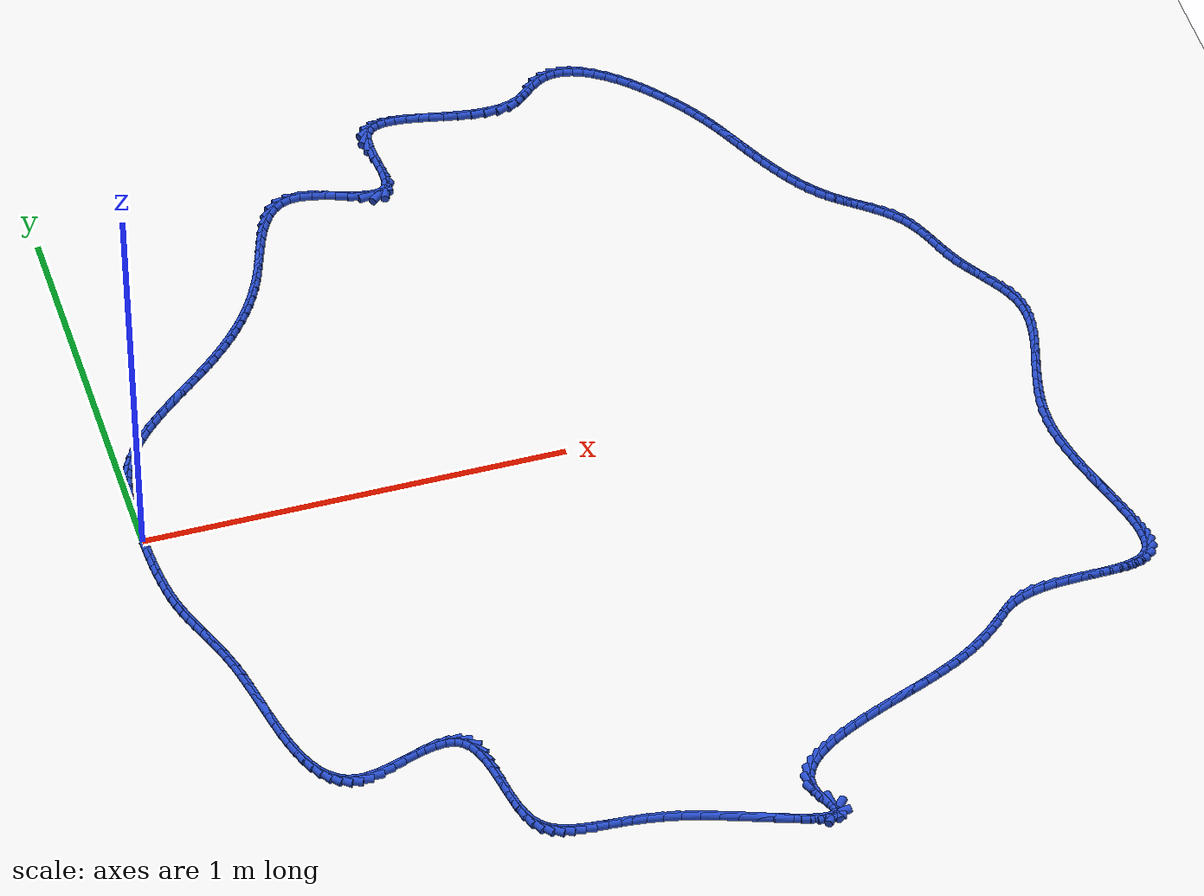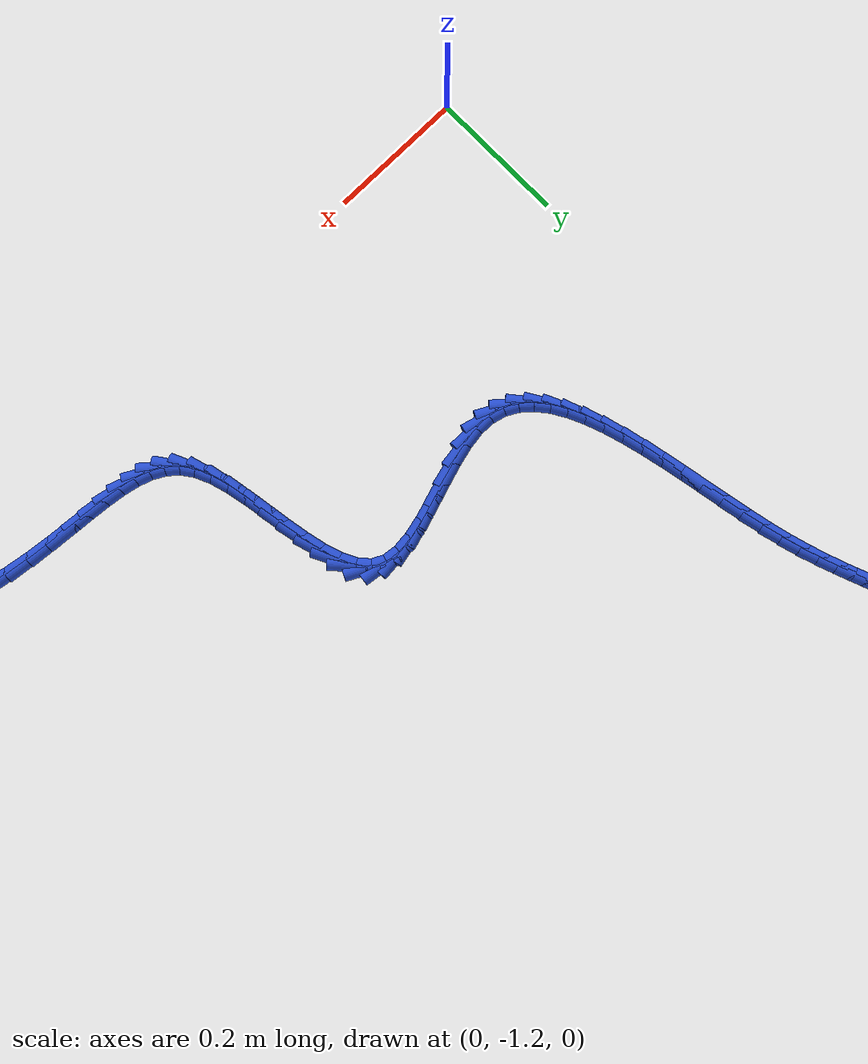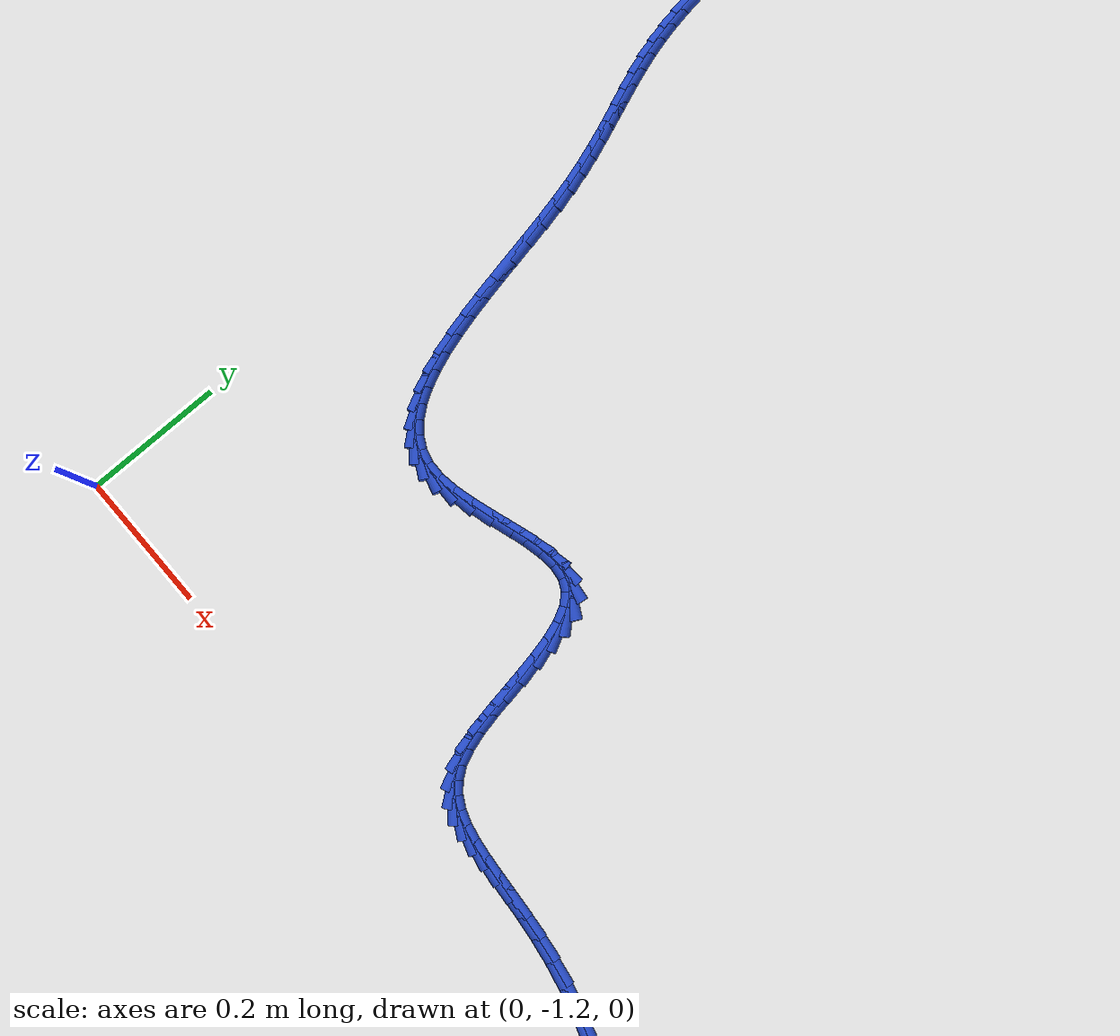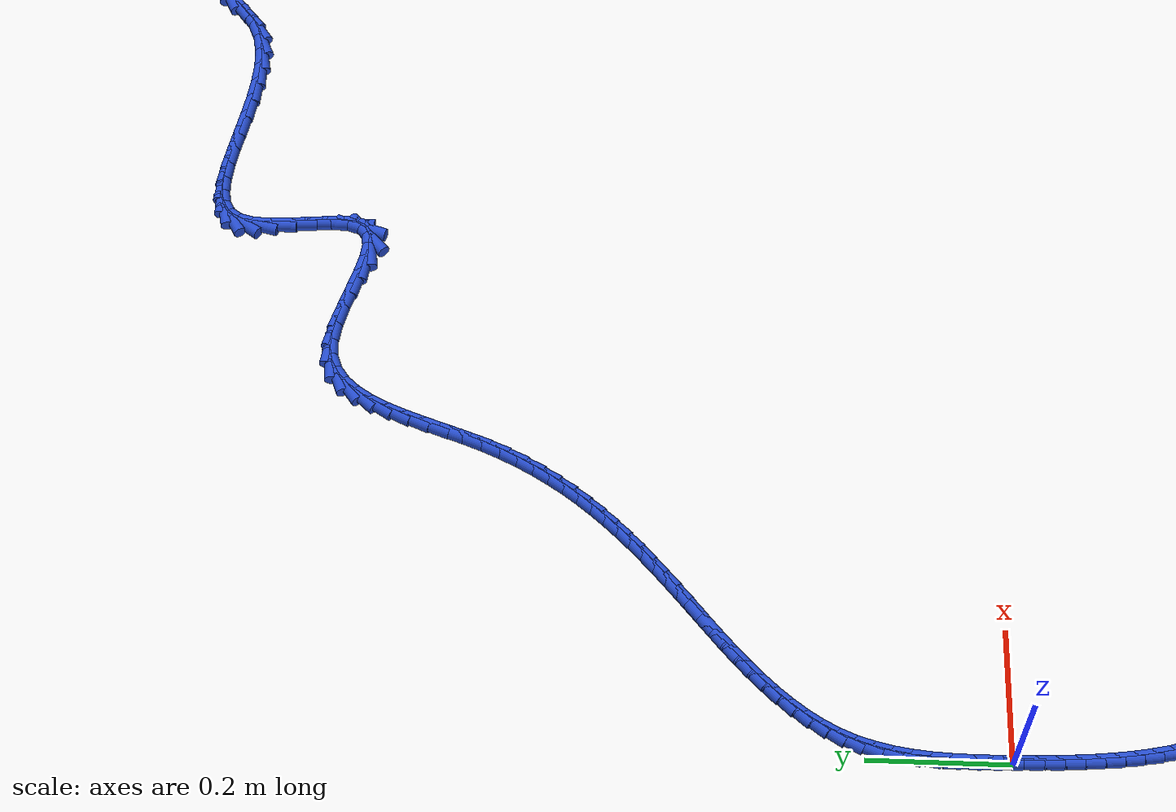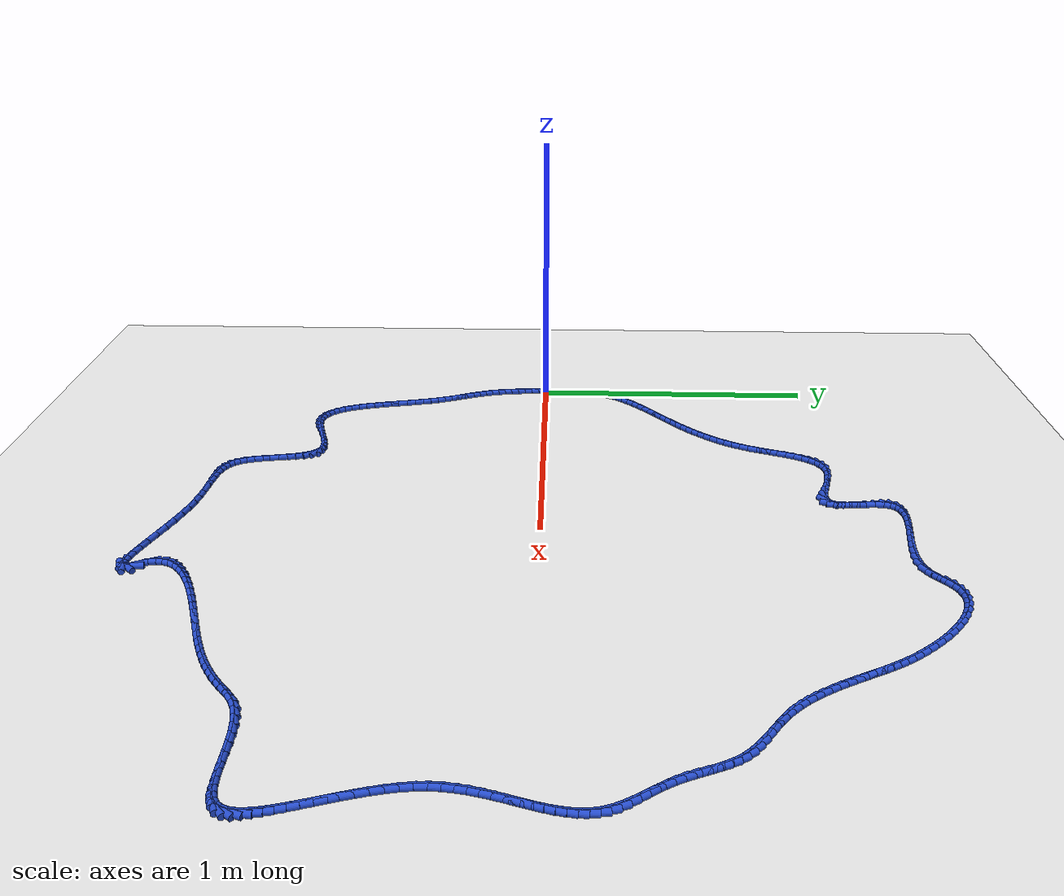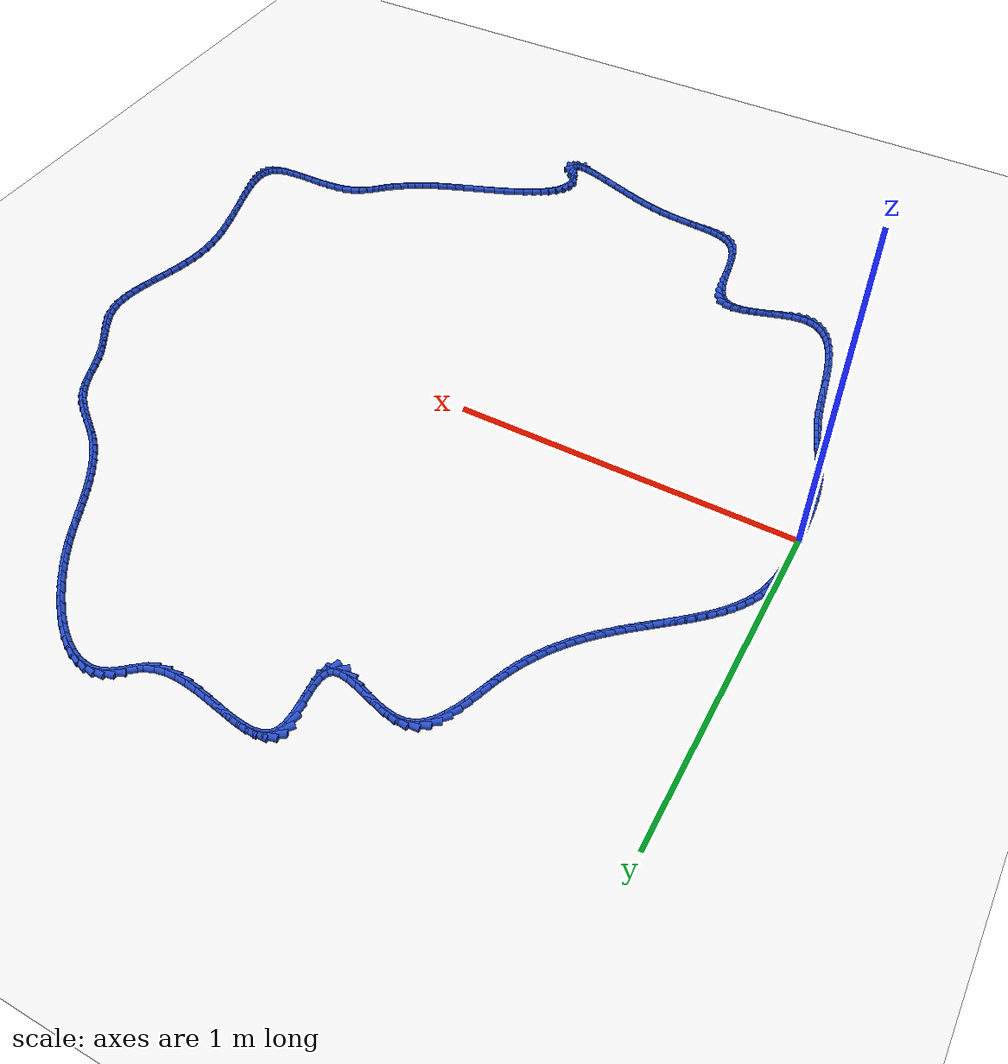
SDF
<sdf version="1.6">
 <world name="default">
  <light name="sun" type="directional">
   <pose>0 0 10 0 -0 0</pose>
   <diffuse>0.8 0.8 0.8 1</diffuse>
   <specular>0.2 0.2 0.2 1</specular>
   <attenuation>
    <range>1000</range>
    <constant>0.9</constant>
    <linear>0.01</linear>
    <quadratic>0.001</quadratic>
   </attenuation>
   <direction>-0.5 0.1 -0.9</direction>
  </light>
  <model name="ground_plane">
   <static>1</static>
   <link name="link">
    <collision name="collision">
     <geometry><plane><normal>0 0 1</normal><size>100 100</size></plane></geometry>
     <surface><friction><ode><mu>100</mu><mu2>50</mu2></ode></friction></surface>
    </collision>
    <visual name="visual">
     <cast_shadows>0</cast_shadows>
     <geometry><plane><normal>0 0 1</normal><size>100 100</size></plane></geometry>
     <material>
      <script><uri>file://media/materials/scripts/gazebo.material</uri><name>Gazebo/WhiteGlow</name></script>
     </material>
    </visual>
   </link>
  </model>
  <gravity>0 0 -9.8</gravity>
  <magnetic_field>6e-06 2.3e-05 -4.2e-05</magnetic_field>
  <atmosphere type="adiabatic"/>
  <physics name="default_physics" default="0" type="ode">
   <max_step_size>0.001</max_step_size>
   <real_time_factor>1</real_time_factor>
   <real_time_update_rate>1000</real_time_update_rate>
  </physics>
  <scene><ambient>0.4 0.4 0.4 1</ambient><background>0.7 0.7 0.7 1</background><shadows>1</shadows></scene>
  <spherical_coordinates>
   <surface_model>EARTH_WGS84</surface_model>
   <latitude_deg>0</latitude_deg>
   <longitude_deg>0</longitude_deg>
   <elevation>0</elevation>
   <heading_deg>0</heading_deg>
  </spherical_coordinates>
  <model name="line">
   <link name="link_0">
    <pose>7.752045533271357e-18 -2.7755575615628914e-17 0.01 0 1.57 -1.5475771578016648</pose>
    <collision name="collision">
     <geometry><cylinder><radius>0.01</radius><length>0.08</length></cylinder></geometry>
    </collision>
    <visual name="visual">
     <material>
      <script><name>Gazebo/Blue</name><uri>file://media/materials/scripts/gazebo.material</uri></script>
     </material>
     <geometry><cylinder><radius>0.01</radius><length>0.08</length></cylinder></geometry>
    </visual>
   </link>
   <link name="link_1">
    <pose>-0.0006423266834701965 0.027658666295119556 0.01 0 1.57 -1.5633790420009965</pose>
    <collision name="collision">
     <geometry><cylinder><radius>0.01</radius><length>0.08</length></cylinder></geometry>
    </collision>
    <visual name="visual">
     <material>
      <script><name>Gazebo/Blue</name><uri>file://media/materials/scripts/gazebo.material</uri></script>
     </material>
     <geometry><cylinder><radius>0.01</radius><length>0.08</length></cylinder></geometry>
    </visual>
   </link>
   <link name="link_2">
    <pose>-0.0008471799076360735 0.05527651744973675 0.01 0 1.57 1.5530773026744242</pose>
    <collision name="collision">
     <geometry><cylinder><radius>0.01</radius><length>0.08</length></cylinder></geometry>
    </collision>
    <visual name="visual">
     <material>
      <script><name>Gazebo/Blue</name><uri>file://media/materials/scripts/gazebo.material</uri></script>
     </material>
     <geometry><cylinder><radius>0.01</radius><length>0.08</length></cylinder></geometry>
    </visual>
   </link>
   <link name="link_3">
    <pose>-0.0003608039724704128 0.08272300825601164 0.01 0 1.57 1.518114131427173</pose>
    <collision name="collision">
     <geometry><cylinder><radius>0.01</radius><length>0.08</length></cylinder></geometry>
    </collision>
    <visual name="visual">
     <material>
      <script><name>Gazebo/Blue</name><uri>file://media/materials/scripts/gazebo.material</uri></script>
     </material>
     <geometry><cylinder><radius>0.01</radius><length>0.08</length></cylinder></geometry>
    </visual>
   </link>
   <link name="link_4">
    <pose>0.0010705568220539968 0.10986759350610421 0.01 0 1.57 1.472651746313057</pose>
    <collision name="collision">
     <geometry><cylinder><radius>0.01</radius><length>0.08</length></cylinder></geometry>
    </collision>
    <visual name="visual">
     <material>
      <script><name>Gazebo/Blue</name><uri>file://media/materials/scripts/gazebo.material</uri></script>
     </material>
     <geometry><cylinder><radius>0.01</radius><length>0.08</length></cylinder></geometry>
    </visual>
   </link>
   <link name="link_5">
    <pose>0.003700658175964367 0.13657972799217455 0.01 0 1.57 1.415919242697305</pose>
    <collision name="collision">
     <geometry><cylinder><radius>0.01</radius><length>0.08</length></cylinder></geometry>
    </collision>
    <visual name="visual">
     <material>
      <script><name>Gazebo/Blue</name><uri>file://media/materials/scripts/gazebo.material</uri></script>
     </material>
     <geometry><cylinder><radius>0.01</radius><length>0.08</length></cylinder></geometry>
    </visual>
   </link>
   <link name="link_6">
    <pose>0.00778325578928791 0.1627288665063827 0.01 0 1.57 1.347189491061914</pose>
    <collision name="collision">
     <geometry><cylinder><radius>0.01</radius><length>0.08</length></cylinder></geometry>
    </collision>
    <visual name="visual">
     <material>
      <script><name>Gazebo/Blue</name><uri>file://media/materials/scripts/gazebo.material</uri></script>
     </material>
     <geometry><cylinder><radius>0.01</radius><length>0.08</length></cylinder></geometry>
    </visual>
   </link>
   <link name="link_7">
    <pose>0.013572105362051827 0.1881844638408887 0.01 0 1.57 1.266007420266653</pose>
    <collision name="collision">
     <geometry><cylinder><radius>0.01</radius><length>0.08</length></cylinder></geometry>
    </collision>
    <visual name="visual">
     <material>
      <script><name>Gazebo/Blue</name><uri>file://media/materials/scripts/gazebo.material</uri></script>
     </material>
     <geometry><cylinder><radius>0.01</radius><length>0.08</length></cylinder></geometry>
    </visual>
   </link>
   <link name="link_8">
    <pose>0.021320962594283347 0.21281597478785255 0.01 0 1.57 1.1732408211207972</pose>
    <collision name="collision">
     <geometry><cylinder><radius>0.01</radius><length>0.08</length></cylinder></geometry>
    </collision>
    <visual name="visual">
     <material>
      <script><name>Gazebo/Blue</name><uri>file://media/materials/scripts/gazebo.material</uri></script>
     </material>
     <geometry><cylinder><radius>0.01</radius><length>0.08</length></cylinder></geometry>
    </visual>
   </link>
   <link name="link_9">
    <pose>0.03126635858407445 0.23650029751691645 0.01 0 1.57 1.081027170066918</pose>
    <collision name="collision">
     <geometry><cylinder><radius>0.01</radius><length>0.08</length></cylinder></geometry>
    </collision>
    <visual name="visual">
     <material>
      <script><name>Gazebo/Blue</name><uri>file://media/materials/scripts/gazebo.material</uri></script>
     </material>
     <geometry><cylinder><radius>0.01</radius><length>0.08</length></cylinder></geometry>
    </visual>
   </link>
   <link name="link_10">
    <pose>0.04338220914261632 0.2592278158225471 0.01 0 1.57 0.9991547696026446</pose>
    <collision name="collision">
     <geometry><cylinder><radius>0.01</radius><length>0.08</length></cylinder></geometry>
    </collision>
    <visual name="visual">
     <material>
      <script><name>Gazebo/Blue</name><uri>file://media/materials/scripts/gazebo.material</uri></script>
     </material>
     <geometry><cylinder><radius>0.01</radius><length>0.08</length></cylinder></geometry>
    </visual>
   </link>
   <link name="link_11">
    <pose>0.05743774080938268 0.28107736718433307 0.01 0 1.57 0.9282244274906649</pose>
    <collision name="collision">
     <geometry><cylinder><radius>0.01</radius><length>0.08</length></cylinder></geometry>
    </collision>
    <visual name="visual">
     <material>
      <script><name>Gazebo/Blue</name><uri>file://media/materials/scripts/gazebo.material</uri></script>
     </material>
     <geometry><cylinder><radius>0.01</radius><length>0.08</length></cylinder></geometry>
    </visual>
   </link>
   <link name="link_12">
    <pose>0.07319676671816215 0.30213012841151066 0.01 0 1.57 0.8680244803851493</pose>
    <collision name="collision">
     <geometry><cylinder><radius>0.01</radius><length>0.08</length></cylinder></geometry>
    </collision>
    <visual name="visual">
     <material>
      <script><name>Gazebo/Blue</name><uri>file://media/materials/scripts/gazebo.material</uri></script>
     </material>
     <geometry><cylinder><radius>0.01</radius><length>0.08</length></cylinder></geometry>
    </visual>
   </link>
   <link name="link_13">
    <pose>0.09042310000274335 0.32246727631331634 0.01 0 1.57 0.8180189828831927</pose>
    <collision name="collision">
     <geometry><cylinder><radius>0.01</radius><length>0.08</length></cylinder></geometry>
    </collision>
    <visual name="visual">
     <material>
      <script><name>Gazebo/Blue</name><uri>file://media/materials/scripts/gazebo.material</uri></script>
     </material>
     <geometry><cylinder><radius>0.01</radius><length>0.08</length></cylinder></geometry>
    </visual>
   </link>
   <link name="link_14">
    <pose>0.1088805537969149 0.3421699876989864 0.01 0 1.57 0.7775506217509162</pose>
    <collision name="collision">
     <geometry><cylinder><radius>0.01</radius><length>0.08</length></cylinder></geometry>
    </collision>
    <visual name="visual">
     <material>
      <script><name>Gazebo/Blue</name><uri>file://media/materials/scripts/gazebo.material</uri></script>
     </material>
     <geometry><cylinder><radius>0.01</radius><length>0.08</length></cylinder></geometry>
    </visual>
   </link>
   <link name="link_15">
    <pose>0.12833294123446545 0.3613194393777572 0.01 0 1.57 0.7459785203252797</pose>
    <collision name="collision">
     <geometry><cylinder><radius>0.01</radius><length>0.08</length></cylinder></geometry>
    </collision>
    <visual name="visual">
     <material>
      <script><name>Gazebo/Blue</name><uri>file://media/materials/scripts/gazebo.material</uri></script>
     </material>
     <geometry><cylinder><radius>0.01</radius><length>0.08</length></cylinder></geometry>
    </visual>
   </link>
   <link name="link_16">
    <pose>0.14854407544918363 0.3799968081588652 0.01 0 1.57 0.7227630919921517</pose>
    <collision name="collision">
     <geometry><cylinder><radius>0.01</radius><length>0.08</length></cylinder></geometry>
    </collision>
    <visual name="visual">
     <material>
      <script><name>Gazebo/Blue</name><uri>file://media/materials/scripts/gazebo.material</uri></script>
     </material>
     <geometry><cylinder><radius>0.01</radius><length>0.08</length></cylinder></geometry>
    </visual>
   </link>
   <link name="link_17">
    <pose>0.16927776957485807 0.39828327085154674 0.01 0 1.57 0.7075154170517273</pose>
    <collision name="collision">
     <geometry><cylinder><radius>0.01</radius><length>0.08</length></cylinder></geometry>
    </collision>
    <visual name="visual">
     <material>
      <script><name>Gazebo/Blue</name><uri>file://media/materials/scripts/gazebo.material</uri></script>
     </material>
     <geometry><cylinder><radius>0.01</radius><length>0.08</length></cylinder></geometry>
    </visual>
   </link>
   <link name="link_18">
    <pose>0.1902978367452774 0.4162600042650382 0.01 0 1.57 0.7000264128743866</pose>
    <collision name="collision">
     <geometry><cylinder><radius>0.01</radius><length>0.08</length></cylinder></geometry>
    </collision>
    <visual name="visual">
     <material>
      <script><name>Gazebo/Blue</name><uri>file://media/materials/scripts/gazebo.material</uri></script>
     </material>
     <geometry><cylinder><radius>0.01</radius><length>0.08</length></cylinder></geometry>
    </visual>
   </link>
   <link name="link_19">
    <pose>0.21136809009423022 0.43400818520857576 0.01 0 1.57 0.7002868148669174</pose>
    <collision name="collision">
     <geometry><cylinder><radius>0.01</radius><length>0.08</length></cylinder></geometry>
    </collision>
    <visual name="visual">
     <material>
      <script><name>Gazebo/Blue</name><uri>file://media/materials/scripts/gazebo.material</uri></script>
     </material>
     <geometry><cylinder><radius>0.01</radius><length>0.08</length></cylinder></geometry>
    </visual>
   </link>
   <link name="link_20">
    <pose>0.23225234275550521 0.45160899049139586 0.01 0 1.57 0.708218803882424</pose>
    <collision name="collision">
     <geometry><cylinder><radius>0.01</radius><length>0.08</length></cylinder></geometry>
    </collision>
    <visual name="visual">
     <material>
      <script><name>Gazebo/Blue</name><uri>file://media/materials/scripts/gazebo.material</uri></script>
     </material>
     <geometry><cylinder><radius>0.01</radius><length>0.08</length></cylinder></geometry>
    </visual>
   </link>
   <link name="link_21">
    <pose>0.2527290090455688 0.4691459502157629 0.01 0 1.57 0.7216131995806573</pose>
    <collision name="collision">
     <geometry><cylinder><radius>0.01</radius><length>0.08</length></cylinder></geometry>
    </collision>
    <visual name="visual">
     <material>
      <script><name>Gazebo/Blue</name><uri>file://media/materials/scripts/gazebo.material</uri></script>
     </material>
     <geometry><cylinder><radius>0.01</radius><length>0.08</length></cylinder></geometry>
    </visual>
   </link>
   <link name="link_22">
    <pose>0.27270494228408215 0.4867232951776731 0.01 0 1.57 0.739277491214392</pose>
    <collision name="collision">
     <geometry><cylinder><radius>0.01</radius><length>0.08</length></cylinder></geometry>
    </collision>
    <visual name="visual">
     <material>
      <script><name>Gazebo/Blue</name><uri>file://media/materials/scripts/gazebo.material</uri></script>
     </material>
     <geometry><cylinder><radius>0.01</radius><length>0.08</length></cylinder></geometry>
    </visual>
   </link>
   <link name="link_23">
    <pose>0.29215370684742287 0.5044560080874104 0.01 0 1.57 0.7612131552611355</pose>
    <collision name="collision">
     <geometry><cylinder><radius>0.01</radius><length>0.08</length></cylinder></geometry>
    </collision>
    <visual name="visual">
     <material>
      <script><name>Gazebo/Blue</name><uri>file://media/materials/scripts/gazebo.material</uri></script>
     </material>
     <geometry><cylinder><radius>0.01</radius><length>0.08</length></cylinder></geometry>
    </visual>
   </link>
   <link name="link_24">
    <pose>0.3110494359465746 0.5224591633351279 0.01 0 1.57 0.7873555005937828</pose>
    <collision name="collision">
     <geometry><cylinder><radius>0.01</radius><length>0.08</length></cylinder></geometry>
    </collision>
    <visual name="visual">
     <material>
      <script><name>Gazebo/Blue</name><uri>file://media/materials/scripts/gazebo.material</uri></script>
     </material>
     <geometry><cylinder><radius>0.01</radius><length>0.08</length></cylinder></geometry>
    </visual>
   </link>
   <link name="link_25">
    <pose>0.3293662627925213 0.5408478353109788 0.01 0 1.57 0.8175499981400233</pose>
    <collision name="collision">
     <geometry><cylinder><radius>0.01</radius><length>0.08</length></cylinder></geometry>
    </collision>
    <visual name="visual">
     <material>
      <script><name>Gazebo/Blue</name><uri>file://media/materials/scripts/gazebo.material</uri></script>
     </material>
     <geometry><cylinder><radius>0.01</radius><length>0.08</length></cylinder></geometry>
    </visual>
   </link>
   <link name="link_26">
    <pose>0.34707832059624644 0.5597370984051162 0.01 0 1.57 0.851542264850933</pose>
    <collision name="collision">
     <geometry><cylinder><radius>0.01</radius><length>0.08</length></cylinder></geometry>
    </collision>
    <visual name="visual">
     <material>
      <script><name>Gazebo/Blue</name><uri>file://media/materials/scripts/gazebo.material</uri></script>
     </material>
     <geometry><cylinder><radius>0.01</radius><length>0.08</length></cylinder></geometry>
    </visual>
   </link>
   <link name="link_27">
    <pose>0.36415974256873374 0.5792420270076929 0.01 0 1.57 0.8889729479813079</pose>
    <collision name="collision">
     <geometry><cylinder><radius>0.01</radius><length>0.08</length></cylinder></geometry>
    </collision>
    <visual name="visual">
     <material>
      <script><name>Gazebo/Blue</name><uri>file://media/materials/scripts/gazebo.material</uri></script>
     </material>
     <geometry><cylinder><radius>0.01</radius><length>0.08</length></cylinder></geometry>
    </visual>
   </link>
   <link name="link_28">
    <pose>0.3805846619209672 0.5994776955088623 0.01 0 1.57 0.9293799062217508</pose>
    <collision name="collision">
     <geometry><cylinder><radius>0.01</radius><length>0.08</length></cylinder></geometry>
    </collision>
    <visual name="visual">
     <material>
      <script><name>Gazebo/Blue</name><uri>file://media/materials/scripts/gazebo.material</uri></script>
     </material>
     <geometry><cylinder><radius>0.01</radius><length>0.08</length></cylinder></geometry>
    </visual>
   </link>
   <link name="link_29">
    <pose>0.39632721186393033 0.6205591782987772 0.01 0 1.57 0.9722094681198448</pose>
    <collision name="collision">
     <geometry><cylinder><radius>0.01</radius><length>0.08</length></cylinder></geometry>
    </collision>
    <visual name="visual">
     <material>
      <script><name>Gazebo/Blue</name><uri>file://media/materials/scripts/gazebo.material</uri></script>
     </material>
     <geometry><cylinder><radius>0.01</radius><length>0.08</length></cylinder></geometry>
    </visual>
   </link>
   <link name="link_30">
    <pose>0.4113615256086067 0.6426015497675905 0.01 0 1.57 1.0168372478420402</pose>
    <collision name="collision">
     <geometry><cylinder><radius>0.01</radius><length>0.08</length></cylinder></geometry>
    </collision>
    <visual name="visual">
     <material>
      <script><name>Gazebo/Blue</name><uri>file://media/materials/scripts/gazebo.material</uri></script>
     </material>
     <geometry><cylinder><radius>0.01</radius><length>0.08</length></cylinder></geometry>
    </visual>
   </link>
   <link name="link_31">
    <pose>0.42566173636598037 0.6657198843054559 0.01 0 1.57 1.0625972129175245</pose>
    <collision name="collision">
     <geometry><cylinder><radius>0.01</radius><length>0.08</length></cylinder></geometry>
    </collision>
    <visual name="visual">
     <material>
      <script><name>Gazebo/Blue</name><uri>file://media/materials/scripts/gazebo.material</uri></script>
     </material>
     <geometry><cylinder><radius>0.01</radius><length>0.08</length></cylinder></geometry>
    </visual>
   </link>
   <link name="link_32">
    <pose>0.43920197734703487 0.6900292563025261 0.01 0 1.57 1.1088158944102549</pose>
    <collision name="collision">
     <geometry><cylinder><radius>0.01</radius><length>0.08</length></cylinder></geometry>
    </collision>
    <visual name="visual">
     <material>
      <script><name>Gazebo/Blue</name><uri>file://media/materials/scripts/gazebo.material</uri></script>
     </material>
     <geometry><cylinder><radius>0.01</radius><length>0.08</length></cylinder></geometry>
    </visual>
   </link>
   <link name="link_33">
    <pose>0.45195638176275393 0.7156447401489539 0.01 0 1.57 1.154847393121973</pose>
    <collision name="collision">
     <geometry><cylinder><radius>0.01</radius><length>0.08</length></cylinder></geometry>
    </collision>
    <visual name="visual">
     <material>
      <script><name>Gazebo/Blue</name><uri>file://media/materials/scripts/gazebo.material</uri></script>
     </material>
     <geometry><cylinder><radius>0.01</radius><length>0.08</length></cylinder></geometry>
    </visual>
   </link>
   <link name="link_34">
    <pose>0.4638990828241213 0.7426814102348929 0.01 0 1.57 1.1991642155798223</pose>
    <collision name="collision">
     <geometry><cylinder><radius>0.01</radius><length>0.08</length></cylinder></geometry>
    </collision>
    <visual name="visual">
     <material>
      <script><name>Gazebo/Blue</name><uri>file://media/materials/scripts/gazebo.material</uri></script>
     </material>
     <geometry><cylinder><radius>0.01</radius><length>0.08</length></cylinder></geometry>
    </visual>
   </link>
   <link name="link_35">
    <pose>0.47502176675619784 0.7712199923471602 0.01 0 1.57 1.2283384621554092</pose>
    <collision name="collision">
     <geometry><cylinder><radius>0.01</radius><length>0.08</length></cylinder></geometry>
    </collision>
    <visual name="visual">
     <material>
      <script><name>Gazebo/Blue</name><uri>file://media/materials/scripts/gazebo.material</uri></script>
     </material>
     <geometry><cylinder><radius>0.01</radius><length>0.08</length></cylinder></geometry>
    </visual>
   </link>
   <link name="link_36">
    <pose>0.4855776636415354 0.800829410357741 0.01 0 1.57 1.234318057412207</pose>
    <collision name="collision">
     <geometry><cylinder><radius>0.01</radius><length>0.08</length></cylinder></geometry>
    </collision>
    <visual name="visual">
     <material>
      <script><name>Gazebo/Blue</name><uri>file://media/materials/scripts/gazebo.material</uri></script>
     </material>
     <geometry><cylinder><radius>0.01</radius><length>0.08</length></cylinder></geometry>
    </visual>
   </link>
   <link name="link_37">
    <pose>0.49602077879622214 0.8306857012631228 0.01 0 1.57 1.2176225340649984</pose>
    <collision name="collision">
     <geometry><cylinder><radius>0.01</radius><length>0.08</length></cylinder></geometry>
    </collision>
    <visual name="visual">
     <material>
      <script><name>Gazebo/Blue</name><uri>file://media/materials/scripts/gazebo.material</uri></script>
     </material>
     <geometry><cylinder><radius>0.01</radius><length>0.08</length></cylinder></geometry>
    </visual>
   </link>
   <link name="link_38">
    <pose>0.5068102498295757 0.8599548589353737 0.01 0 1.57 1.176261530008575</pose>
    <collision name="collision">
     <geometry><cylinder><radius>0.01</radius><length>0.08</length></cylinder></geometry>
    </collision>
    <visual name="visual">
     <material>
      <script><name>Gazebo/Blue</name><uri>file://media/materials/scripts/gazebo.material</uri></script>
     </material>
     <geometry><cylinder><radius>0.01</radius><length>0.08</length></cylinder></geometry>
    </visual>
   </link>
   <link name="link_39">
    <pose>0.5184052143509137 0.8878028772465615 0.01 0 1.57 1.1051763924258355</pose>
    <collision name="collision">
     <geometry><cylinder><radius>0.01</radius><length>0.08</length></cylinder></geometry>
    </collision>
    <visual name="visual">
     <material>
      <script><name>Gazebo/Blue</name><uri>file://media/materials/scripts/gazebo.material</uri></script>
     </material>
     <geometry><cylinder><radius>0.01</radius><length>0.08</length></cylinder></geometry>
    </visual>
   </link>
   <link name="link_40">
    <pose>0.5312648099695532 0.9133957500687531 0.01 0 1.57 0.9957985428732469</pose>
    <collision name="collision">
     <geometry><cylinder><radius>0.01</radius><length>0.08</length></cylinder></geometry>
    </collision>
    <visual name="visual">
     <material>
      <script><name>Gazebo/Blue</name><uri>file://media/materials/scripts/gazebo.material</uri></script>
     </material>
     <geometry><cylinder><radius>0.01</radius><length>0.08</length></cylinder></geometry>
    </visual>
   </link>
   <link name="link_41">
    <pose>0.5458481742948121 0.9358994712740168 0.01 0 1.57 0.8366814556859311</pose>
    <collision name="collision">
     <geometry><cylinder><radius>0.01</radius><length>0.08</length></cylinder></geometry>
    </collision>
    <visual name="visual">
     <material>
      <script><name>Gazebo/Blue</name><uri>file://media/materials/scripts/gazebo.material</uri></script>
     </material>
     <geometry><cylinder><radius>0.01</radius><length>0.08</length></cylinder></geometry>
    </visual>
   </link>
   <link name="link_42">
    <pose>0.5626144449360075 0.9544800347344197 0.01 0 1.57 0.6188943193623295</pose>
    <collision name="collision">
     <geometry><cylinder><radius>0.01</radius><length>0.08</length></cylinder></geometry>
    </collision>
    <visual name="visual">
     <material>
      <script><name>Gazebo/Blue</name><uri>file://media/materials/scripts/gazebo.material</uri></script>
     </material>
     <geometry><cylinder><radius>0.01</radius><length>0.08</length></cylinder></geometry>
    </visual>
   </link>
   <link name="link_43">
    <pose>0.5820227595024572 0.9683034343220294 0.01 0 1.57 0.35061228349243506</pose>
    <collision name="collision">
     <geometry><cylinder><radius>0.01</radius><length>0.08</length></cylinder></geometry>
    </collision>
    <visual name="visual">
     <material>
      <script><name>Gazebo/Blue</name><uri>file://media/materials/scripts/gazebo.material</uri></script>
     </material>
     <geometry><cylinder><radius>0.01</radius><length>0.08</length></cylinder></geometry>
    </visual>
   </link>
   <link name="link_44">
    <pose>0.6045322556034789 0.9765356639089144 0.01 0 1.57 0.07149451687938835</pose>
    <collision name="collision">
     <geometry><cylinder><radius>0.01</radius><length>0.08</length></cylinder></geometry>
    </collision>
    <visual name="visual">
     <material>
      <script><name>Gazebo/Blue</name><uri>file://media/materials/scripts/gazebo.material</uri></script>
     </material>
     <geometry><cylinder><radius>0.01</radius><length>0.08</length></cylinder></geometry>
    </visual>
   </link>
   <link name="link_45">
    <pose>0.6305651963571177 0.9784000541030357 0.01 0 1.57 -0.13415704344314294</pose>
    <collision name="collision">
     <geometry><cylinder><radius>0.01</radius><length>0.08</length></cylinder></geometry>
    </collision>
    <visual name="visual">
     <material>
      <script><name>Gazebo/Blue</name><uri>file://media/materials/scripts/gazebo.material</uri></script>
     </material>
     <geometry><cylinder><radius>0.01</radius><length>0.08</length></cylinder></geometry>
    </visual>
   </link>
   <link name="link_46">
    <pose>0.6596748215145456 0.9744711938363129 0.01 0 1.57 -0.24690721367991458</pose>
    <collision name="collision">
     <geometry><cylinder><radius>0.01</radius><length>0.08</length></cylinder></geometry>
    </collision>
    <visual name="visual">
     <material>
      <script><name>Gazebo/Blue</name><uri>file://media/materials/scripts/gazebo.material</uri></script>
     </material>
     <geometry><cylinder><radius>0.01</radius><length>0.08</length></cylinder></geometry>
    </visual>
   </link>
   <link name="link_47">
    <pose>0.690533569530157 0.9666932440560893 0.01 0 1.57 -0.2987690628109599</pose>
    <collision name="collision">
     <geometry><cylinder><radius>0.01</radius><length>0.08</length></cylinder></geometry>
    </collision>
    <visual name="visual">
     <material>
      <script><name>Gazebo/Blue</name><uri>file://media/materials/scripts/gazebo.material</uri></script>
     </material>
     <geometry><cylinder><radius>0.01</radius><length>0.08</length></cylinder></geometry>
    </visual>
   </link>
   <link name="link_48">
    <pose>0.7217746486472709 0.9570713653919816 0.01 0 1.57 -0.3030490702650331</pose>
    <collision name="collision">
     <geometry><cylinder><radius>0.01</radius><length>0.08</length></cylinder></geometry>
    </collision>
    <visual name="visual">
     <material>
      <script><name>Gazebo/Blue</name><uri>file://media/materials/scripts/gazebo.material</uri></script>
     </material>
     <geometry><cylinder><radius>0.01</radius><length>0.08</length></cylinder></geometry>
    </visual>
   </link>
   <link name="link_49">
    <pose>0.7520312671092055 0.9476107184736068 0.01 0 1.57 -0.25567198159813986</pose>
    <collision name="collision">
     <geometry><cylinder><radius>0.01</radius><length>0.08</length></cylinder></geometry>
    </collision>
    <visual name="visual">
     <material>
      <script><name>Gazebo/Blue</name><uri>file://media/materials/scripts/gazebo.material</uri></script>
     </material>
     <geometry><cylinder><radius>0.01</radius><length>0.08</length></cylinder></geometry>
    </visual>
   </link>
   <link name="link_50">
    <pose>0.7799366331592797 0.9403164639305817 0.01 0 1.57 -0.12839466978453928</pose>
    <collision name="collision">
     <geometry><cylinder><radius>0.01</radius><length>0.08</length></cylinder></geometry>
    </collision>
    <visual name="visual">
     <material>
      <script><name>Gazebo/Blue</name><uri>file://media/materials/scripts/gazebo.material</uri></script>
     </material>
     <geometry><cylinder><radius>0.01</radius><length>0.08</length></cylinder></geometry>
    </visual>
   </link>
   <link name="link_51">
    <pose>0.804123955040812 0.9371937623925232 0.01 0 1.57 0.15853348989814392</pose>
    <collision name="collision">
     <geometry><cylinder><radius>0.01</radius><length>0.08</length></cylinder></geometry>
    </collision>
    <visual name="visual">
     <material>
      <script><name>Gazebo/Blue</name><uri>file://media/materials/scripts/gazebo.material</uri></script>
     </material>
     <geometry><cylinder><radius>0.01</radius><length>0.08</length></cylinder></geometry>
    </visual>
   </link>
   <link name="link_52">
    <pose>0.8232264409971214 0.940247774489048 0.01 0 1.57 0.7243325198861073</pose>
    <collision name="collision">
     <geometry><cylinder><radius>0.01</radius><length>0.08</length></cylinder></geometry>
    </collision>
    <visual name="visual">
     <material>
      <script><name>Gazebo/Blue</name><uri>file://media/materials/scripts/gazebo.material</uri></script>
     </material>
     <geometry><cylinder><radius>0.01</radius><length>0.08</length></cylinder></geometry>
    </visual>
   </link>
   <link name="link_53">
    <pose>0.8358965639742957 0.9514578240350775 0.01 0 1.57 1.2713635657957663</pose>
    <collision name="collision">
     <geometry><cylinder><radius>0.01</radius><length>0.08</length></cylinder></geometry>
    </collision>
    <visual name="visual">
     <material>
      <script><name>Gazebo/Blue</name><uri>file://media/materials/scripts/gazebo.material</uri></script>
     </material>
     <geometry><cylinder><radius>0.01</radius><length>0.08</length></cylinder></geometry>
    </visual>
   </link>
   <link name="link_54">
    <pose>0.8419886168684114 0.9711914166039304 0.01 0 1.57 1.5226162879572358</pose>
    <collision name="collision">
     <geometry><cylinder><radius>0.01</radius><length>0.08</length></cylinder></geometry>
    </collision>
    <visual name="visual">
     <material>
      <script><name>Gazebo/Blue</name><uri>file://media/materials/scripts/gazebo.material</uri></script>
     </material>
     <geometry><cylinder><radius>0.01</radius><length>0.08</length></cylinder></geometry>
    </visual>
   </link>
   <link name="link_55">
    <pose>0.8432466191284564 0.9972816550660388 0.01 0 1.57 -1.5154167701613044</pose>
    <collision name="collision">
     <geometry><cylinder><radius>0.01</radius><length>0.08</length></cylinder></geometry>
    </collision>
    <visual name="visual">
     <material>
      <script><name>Gazebo/Blue</name><uri>file://media/materials/scripts/gazebo.material</uri></script>
     </material>
     <geometry><cylinder><radius>0.01</radius><length>0.08</length></cylinder></geometry>
    </visual>
   </link>
   <link name="link_56">
    <pose>0.8415803331607533 1.0273393564810083 0.01 0 1.57 -1.4862589606676913</pose>
    <collision name="collision">
     <geometry><cylinder><radius>0.01</radius><length>0.08</length></cylinder></geometry>
    </collision>
    <visual name="visual">
     <material>
      <script><name>Gazebo/Blue</name><uri>file://media/materials/scripts/gazebo.material</uri></script>
     </material>
     <geometry><cylinder><radius>0.01</radius><length>0.08</length></cylinder></geometry>
    </visual>
   </link>
   <link name="link_57">
    <pose>0.8388995213716254 1.058975337908444 0.01 0 1.57 -1.512934930191467</pose>
    <collision name="collision">
     <geometry><cylinder><radius>0.01</radius><length>0.08</length></cylinder></geometry>
    </collision>
    <visual name="visual">
     <material>
      <script><name>Gazebo/Blue</name><uri>file://media/materials/scripts/gazebo.material</uri></script>
     </material>
     <geometry><cylinder><radius>0.01</radius><length>0.08</length></cylinder></geometry>
    </visual>
   </link>
   <link name="link_58">
    <pose>0.8371139461673955 1.089800416407951 0.01 0 1.57 1.5339108355819402</pose>
    <collision name="collision">
     <geometry><cylinder><radius>0.01</radius><length>0.08</length></cylinder></geometry>
    </collision>
    <visual name="visual">
     <material>
      <script><name>Gazebo/Blue</name><uri>file://media/materials/scripts/gazebo.material</uri></script>
     </material>
     <geometry><cylinder><radius>0.01</radius><length>0.08</length></cylinder></geometry>
    </visual>
   </link>
   <link name="link_59">
    <pose>0.8381333699543873 1.1174254090391353 0.01 0 1.57 1.3171862648424288</pose>
    <collision name="collision">
     <geometry><cylinder><radius>0.01</radius><length>0.08</length></cylinder></geometry>
    </collision>
    <visual name="visual">
     <material>
      <script><name>Gazebo/Blue</name><uri>file://media/materials/scripts/gazebo.material</uri></script>
     </material>
     <geometry><cylinder><radius>0.01</radius><length>0.08</length></cylinder></geometry>
    </visual>
   </link>
   <link name="link_60">
    <pose>0.8438505186536222 1.1394830824033557 0.01 0 1.57 0.9351210997044489</pose>
    <collision name="collision">
     <geometry><cylinder><radius>0.01</radius><length>0.08</length></cylinder></geometry>
    </collision>
    <visual name="visual">
     <material>
      <script><name>Gazebo/Blue</name><uri>file://media/materials/scripts/gazebo.material</uri></script>
     </material>
     <geometry><cylinder><radius>0.01</radius><length>0.08</length></cylinder></geometry>
    </visual>
   </link>
   <link name="link_61">
    <pose>0.8551907611300613 1.1548525308342499 0.01 0 1.57 0.5223403211299958</pose>
    <collision name="collision">
     <geometry><cylinder><radius>0.01</radius><length>0.08</length></cylinder></geometry>
    </collision>
    <visual name="visual">
     <material>
      <script><name>Gazebo/Blue</name><uri>file://media/materials/scripts/gazebo.material</uri></script>
     </material>
     <geometry><cylinder><radius>0.01</radius><length>0.08</length></cylinder></geometry>
    </visual>
   </link>
   <link name="link_62">
    <pose>0.871610769142672 1.1643050950930323 0.01 0 1.57 0.21113501775359536</pose>
    <collision name="collision">
     <geometry><cylinder><radius>0.01</radius><length>0.08</length></cylinder></geometry>
    </collision>
    <visual name="visual">
     <material>
      <script><name>Gazebo/Blue</name><uri>file://media/materials/scripts/gazebo.material</uri></script>
     </material>
     <geometry><cylinder><radius>0.01</radius><length>0.08</length></cylinder></geometry>
    </visual>
   </link>
   <link name="link_63">
    <pose>0.8924443968549333 1.1687703522139747 0.01 0 1.57 0.016577356583463376</pose>
    <collision name="collision">
     <geometry><cylinder><radius>0.01</radius><length>0.08</length></cylinder></geometry>
    </collision>
    <visual name="visual">
     <material>
      <script><name>Gazebo/Blue</name><uri>file://media/materials/scripts/gazebo.material</uri></script>
     </material>
     <geometry><cylinder><radius>0.01</radius><length>0.08</length></cylinder></geometry>
    </visual>
   </link>
   <link name="link_64">
    <pose>0.9170254984303244 1.1691778792313519 0.01 0 1.57 -0.09803565814863689</pose>
    <collision name="collision">
     <geometry><cylinder><radius>0.01</radius><length>0.08</length></cylinder></geometry>
    </collision>
    <visual name="visual">
     <material>
      <script><name>Gazebo/Blue</name><uri>file://media/materials/scripts/gazebo.material</uri></script>
     </material>
     <geometry><cylinder><radius>0.01</radius><length>0.08</length></cylinder></geometry>
    </visual>
   </link>
   <link name="link_65">
    <pose>0.9446879280323245 1.166457253179436 0.01 0 1.57 -0.16211500192336245</pose>
    <collision name="collision">
     <geometry><cylinder><radius>0.01</radius><length>0.08</length></cylinder></geometry>
    </collision>
    <visual name="visual">
     <material>
      <script><name>Gazebo/Blue</name><uri>file://media/materials/scripts/gazebo.material</uri></script>
     </material>
     <geometry><cylinder><radius>0.01</radius><length>0.08</length></cylinder></geometry>
    </visual>
   </link>
   <link name="link_66">
    <pose>0.9747655398244128 1.1615380510925002 0.01 0 1.57 -0.192038515866562</pose>
    <collision name="collision">
     <geometry><cylinder><radius>0.01</radius><length>0.08</length></cylinder></geometry>
    </collision>
    <visual name="visual">
     <material>
      <script><name>Gazebo/Blue</name><uri>file://media/materials/scripts/gazebo.material</uri></script>
     </material>
     <geometry><cylinder><radius>0.01</radius><length>0.08</length></cylinder></geometry>
    </visual>
   </link>
   <link name="link_67">
    <pose>1.006592187970068 1.155349850004818 0.01 0 1.57 -0.19580898868376148</pose>
    <collision name="collision">
     <geometry><cylinder><radius>0.01</radius><length>0.08</length></cylinder></geometry>
    </collision>
    <visual name="visual">
     <material>
      <script><name>Gazebo/Blue</name><uri>file://media/materials/scripts/gazebo.material</uri></script>
     </material>
     <geometry><cylinder><radius>0.01</radius><length>0.08</length></cylinder></geometry>
    </visual>
   </link>
   <link name="link_68">
    <pose>1.0395017266327704 1.148822226950663 0.01 0 1.57 -0.17631178104226214</pose>
    <collision name="collision">
     <geometry><cylinder><radius>0.01</radius><length>0.08</length></cylinder></geometry>
    </collision>
    <visual name="visual">
     <material>
      <script><name>Gazebo/Blue</name><uri>file://media/materials/scripts/gazebo.material</uri></script>
     </material>
     <geometry><cylinder><radius>0.01</radius><length>0.08</length></cylinder></geometry>
    </visual>
   </link>
   <link name="link_69">
    <pose>1.072828009975998 1.1428847589643072 0.01 0 1.57 -0.13277386180010536</pose>
    <collision name="collision">
     <geometry><cylinder><radius>0.01</radius><length>0.08</length></cylinder></geometry>
    </collision>
    <visual name="visual">
     <material>
      <script><name>Gazebo/Blue</name><uri>file://media/materials/scripts/gazebo.material</uri></script>
     </material>
     <geometry><cylinder><radius>0.01</radius><length>0.08</length></cylinder></geometry>
    </visual>
   </link>
   <link name="link_70">
    <pose>1.10590489216323 1.1384670230800245 0.01 0 1.57 -0.061128504838677725</pose>
    <collision name="collision">
     <geometry><cylinder><radius>0.01</radius><length>0.08</length></cylinder></geometry>
    </collision>
    <visual name="visual">
     <material>
      <script><name>Gazebo/Blue</name><uri>file://media/materials/scripts/gazebo.material</uri></script>
     </material>
     <geometry><cylinder><radius>0.01</radius><length>0.08</length></cylinder></geometry>
    </visual>
   </link>
   <link name="link_71">
    <pose>1.138066227357946 1.1364985963320884 0.01 0 1.57 0.046091463732011284</pose>
    <collision name="collision">
     <geometry><cylinder><radius>0.01</radius><length>0.08</length></cylinder></geometry>
    </collision>
    <visual name="visual">
     <material>
      <script><name>Gazebo/Blue</name><uri>file://media/materials/scripts/gazebo.material</uri></script>
     </material>
     <geometry><cylinder><radius>0.01</radius><length>0.08</length></cylinder></geometry>
    </visual>
   </link>
   <link name="link_72">
    <pose>1.1686458697236253 1.137909055754771 0.01 0 1.57 0.19917879251803572</pose>
    <collision name="collision">
     <geometry><cylinder><radius>0.01</radius><length>0.08</length></cylinder></geometry>
    </collision>
    <visual name="visual">
     <material>
      <script><name>Gazebo/Blue</name><uri>file://media/materials/scripts/gazebo.material</uri></script>
     </material>
     <geometry><cylinder><radius>0.01</radius><length>0.08</length></cylinder></geometry>
    </visual>
   </link>
   <link name="link_73">
    <pose>1.196977673423747 1.1436279783823466 0.01 0 1.57 0.40683771690887793</pose>
    <collision name="collision">
     <geometry><cylinder><radius>0.01</radius><length>0.08</length></cylinder></geometry>
    </collision>
    <visual name="visual">
     <material>
      <script><name>Gazebo/Blue</name><uri>file://media/materials/scripts/gazebo.material</uri></script>
     </material>
     <geometry><cylinder><radius>0.01</radius><length>0.08</length></cylinder></geometry>
    </visual>
   </link>
   <link name="link_74">
    <pose>1.222397399825159 1.154580746220835 0.01 0 1.57 0.6162461585901174</pose>
    <collision name="collision">
     <geometry><cylinder><radius>0.01</radius><length>0.08</length></cylinder></geometry>
    </collision>
    <visual name="visual">
     <material>
      <script><name>Gazebo/Blue</name><uri>file://media/materials/scripts/gazebo.material</uri></script>
     </material>
     <geometry><cylinder><radius>0.01</radius><length>0.08</length></cylinder></geometry>
    </visual>
   </link>
   <link name="link_75">
    <pose>1.2448052333579558 1.1704512529613882 0.01 0 1.57 0.7032850705173879</pose>
    <collision name="collision">
     <geometry><cylinder><radius>0.01</radius><length>0.08</length></cylinder></geometry>
    </collision>
    <visual name="visual">
     <material>
      <script><name>Gazebo/Blue</name><uri>file://media/materials/scripts/gazebo.material</uri></script>
     </material>
     <geometry><cylinder><radius>0.01</radius><length>0.08</length></cylinder></geometry>
    </visual>
   </link>
   <link name="link_76">
    <pose>1.2654501981878739 1.1879565242143324 0.01 0 1.57 0.6490485500279756</pose>
    <collision name="collision">
     <geometry><cylinder><radius>0.01</radius><length>0.08</length></cylinder></geometry>
    </collision>
    <visual name="visual">
     <material>
      <script><name>Gazebo/Blue</name><uri>file://media/materials/scripts/gazebo.material</uri></script>
     </material>
     <geometry><cylinder><radius>0.01</radius><length>0.08</length></cylinder></geometry>
    </visual>
   </link>
   <link name="link_77">
    <pose>1.285778560560118 1.2033797377322317 0.01 0 1.57 0.44733172068689386</pose>
    <collision name="collision">
     <geometry><cylinder><radius>0.01</radius><length>0.08</length></cylinder></geometry>
    </collision>
    <visual name="visual">
     <material>
      <script><name>Gazebo/Blue</name><uri>file://media/materials/scripts/gazebo.material</uri></script>
     </material>
     <geometry><cylinder><radius>0.01</radius><length>0.08</length></cylinder></geometry>
    </visual>
   </link>
   <link name="link_78">
    <pose>1.3070137638399724 1.2135677170768848 0.01 0 1.57 0.20257526460954614</pose>
    <collision name="collision">
     <geometry><cylinder><radius>0.01</radius><length>0.08</length></cylinder></geometry>
    </collision>
    <visual name="visual">
     <material>
      <script><name>Gazebo/Blue</name><uri>file://media/materials/scripts/gazebo.material</uri></script>
     </material>
     <geometry><cylinder><radius>0.01</radius><length>0.08</length></cylinder></geometry>
    </visual>
   </link>
   <link name="link_79">
    <pose>1.3292825164002517 1.2181415524498738 0.01 0 1.57 -0.024553526507848977</pose>
    <collision name="collision">
     <geometry><cylinder><radius>0.01</radius><length>0.08</length></cylinder></geometry>
    </collision>
    <visual name="visual">
     <material>
      <script><name>Gazebo/Blue</name><uri>file://media/materials/scripts/gazebo.material</uri></script>
     </material>
     <geometry><cylinder><radius>0.01</radius><length>0.08</length></cylinder></geometry>
    </visual>
   </link>
   <link name="link_80">
    <pose>1.3523746665528644 1.2175744447592558 0.01 0 1.57 -0.21733293142520654</pose>
    <collision name="collision">
     <geometry><cylinder><radius>0.01</radius><length>0.08</length></cylinder></geometry>
    </collision>
    <visual name="visual">
     <material>
      <script><name>Gazebo/Blue</name><uri>file://media/materials/scripts/gazebo.material</uri></script>
     </material>
     <geometry><cylinder><radius>0.01</radius><length>0.08</length></cylinder></geometry>
    </visual>
   </link>
   <link name="link_81">
    <pose>1.3760799721058283 1.2123398238489111 0.01 0 1.57 -0.3728097742965832</pose>
    <collision name="collision">
     <geometry><cylinder><radius>0.01</radius><length>0.08</length></cylinder></geometry>
    </collision>
    <visual name="visual">
     <material>
      <script><name>Gazebo/Blue</name><uri>file://media/materials/scripts/gazebo.material</uri></script>
     </material>
     <geometry><cylinder><radius>0.01</radius><length>0.08</length></cylinder></geometry>
    </visual>
   </link>
   <link name="link_82">
    <pose>1.4001881908671605 1.2029111195627187 0.01 0 1.57 -0.4959891873836714</pose>
    <collision name="collision">
     <geometry><cylinder><radius>0.01</radius><length>0.08</length></cylinder></geometry>
    </collision>
    <visual name="visual">
     <material>
      <script><name>Gazebo/Blue</name><uri>file://media/materials/scripts/gazebo.material</uri></script>
     </material>
     <geometry><cylinder><radius>0.01</radius><length>0.08</length></cylinder></geometry>
    </visual>
   </link>
   <link name="link_83">
    <pose>1.4244890806448776 1.1897617617445584 0.01 0 1.57 -0.5939007642213687</pose>
    <collision name="collision">
     <geometry><cylinder><radius>0.01</radius><length>0.08</length></cylinder></geometry>
    </collision>
    <visual name="visual">
     <material>
      <script><name>Gazebo/Blue</name><uri>file://media/materials/scripts/gazebo.material</uri></script>
     </material>
     <geometry><cylinder><radius>0.01</radius><length>0.08</length></cylinder></geometry>
    </visual>
   </link>
   <link name="link_84">
    <pose>1.4487723992469972 1.1733651802383098 0.01 0 1.57 -0.6728616490798006</pose>
    <collision name="collision">
     <geometry><cylinder><radius>0.01</radius><length>0.08</length></cylinder></geometry>
    </collision>
    <visual name="visual">
     <material>
      <script><name>Gazebo/Blue</name><uri>file://media/materials/scripts/gazebo.material</uri></script>
     </material>
     <geometry><cylinder><radius>0.01</radius><length>0.08</length></cylinder></geometry>
    </visual>
   </link>
   <link name="link_85">
    <pose>1.4728279044815369 1.1541948048878525 0.01 0 1.57 -0.7378227231635639</pose>
    <collision name="collision">
     <geometry><cylinder><radius>0.01</radius><length>0.08</length></cylinder></geometry>
    </collision>
    <visual name="visual">
     <material>
      <script><name>Gazebo/Blue</name><uri>file://media/materials/scripts/gazebo.material</uri></script>
     </material>
     <geometry><cylinder><radius>0.01</radius><length>0.08</length></cylinder></geometry>
    </visual>
   </link>
   <link name="link_86">
    <pose>1.4964453541565133 1.1327240655370656 0.01 0 1.57 -0.7924986303031897</pose>
    <collision name="collision">
     <geometry><cylinder><radius>0.01</radius><length>0.08</length></cylinder></geometry>
    </collision>
    <visual name="visual">
     <material>
      <script><name>Gazebo/Blue</name><uri>file://media/materials/scripts/gazebo.material</uri></script>
     </material>
     <geometry><cylinder><radius>0.01</radius><length>0.08</length></cylinder></geometry>
    </visual>
   </link>
   <link name="link_87">
    <pose>1.519414506079944 1.1094263920298284 0.01 0 1.57 -0.8396747547925982</pose>
    <collision name="collision">
     <geometry><cylinder><radius>0.01</radius><length>0.08</length></cylinder></geometry>
    </collision>
    <visual name="visual">
     <material>
      <script><name>Gazebo/Blue</name><uri>file://media/materials/scripts/gazebo.material</uri></script>
     </material>
     <geometry><cylinder><radius>0.01</radius><length>0.08</length></cylinder></geometry>
    </visual>
   </link>
   <link name="link_88">
    <pose>1.541525118059846 1.084775214210021 0.01 0 1.57 -0.8814964665037323</pose>
    <collision name="collision">
     <geometry><cylinder><radius>0.01</radius><length>0.08</length></cylinder></geometry>
    </collision>
    <visual name="visual">
     <material>
      <script><name>Gazebo/Blue</name><uri>file://media/materials/scripts/gazebo.material</uri></script>
     </material>
     <geometry><cylinder><radius>0.01</radius><length>0.08</length></cylinder></geometry>
    </visual>
   </link>
   <link name="link_89">
    <pose>1.5625669479042361 1.0592439619215226 0.01 0 1.57 -0.9197050098906521</pose>
    <collision name="collision">
     <geometry><cylinder><radius>0.01</radius><length>0.08</length></cylinder></geometry>
    </collision>
    <visual name="visual">
     <material>
      <script><name>Gazebo/Blue</name><uri>file://media/materials/scripts/gazebo.material</uri></script>
     </material>
     <geometry><cylinder><radius>0.01</radius><length>0.08</length></cylinder></geometry>
    </visual>
   </link>
   <link name="link_90">
    <pose>1.5823297534211325 1.033306065008213 0.01 0 1.57 -0.9558347476576019</pose>
    <collision name="collision">
     <geometry><cylinder><radius>0.01</radius><length>0.08</length></cylinder></geometry>
    </collision>
    <visual name="visual">
     <material>
      <script><name>Gazebo/Blue</name><uri>file://media/materials/scripts/gazebo.material</uri></script>
     </material>
     <geometry><cylinder><radius>0.01</radius><length>0.08</length></cylinder></geometry>
    </visual>
   </link>
   <link name="link_91">
    <pose>1.600603292418552 1.0074349533139708 0.01 0 1.57 -0.9914035154743359</pose>
    <collision name="collision">
     <geometry><cylinder><radius>0.01</radius><length>0.08</length></cylinder></geometry>
    </collision>
    <visual name="visual">
     <material>
      <script><name>Gazebo/Blue</name><uri>file://media/materials/scripts/gazebo.material</uri></script>
     </material>
     <geometry><cylinder><radius>0.01</radius><length>0.08</length></cylinder></geometry>
    </visual>
   </link>
   <link name="link_92">
    <pose>1.6171773227045119 0.9821040566826769 0.01 0 1.57 -1.027548412618177</pose>
    <collision name="collision">
     <geometry><cylinder><radius>0.01</radius><length>0.08</length></cylinder></geometry>
    </collision>
    <visual name="visual">
     <material>
      <script><name>Gazebo/Blue</name><uri>file://media/materials/scripts/gazebo.material</uri></script>
     </material>
     <geometry><cylinder><radius>0.01</radius><length>0.08</length></cylinder></geometry>
    </visual>
   </link>
   <link name="link_93">
    <pose>1.6319144653663702 0.9576988819626961 0.01 0 1.57 -1.0612299455735912</pose>
    <collision name="collision">
     <geometry><cylinder><radius>0.01</radius><length>0.08</length></cylinder></geometry>
    </collision>
    <visual name="visual">
     <material>
      <script><name>Gazebo/Blue</name><uri>file://media/materials/scripts/gazebo.material</uri></script>
     </material>
     <geometry><cylinder><radius>0.01</radius><length>0.08</length></cylinder></geometry>
    </visual>
   </link>
   <link name="link_94">
    <pose>1.6451126265496645 0.934079684235486 0.01 0 1.57 -1.0888642648271958</pose>
    <collision name="collision">
     <geometry><cylinder><radius>0.01</radius><length>0.08</length></cylinder></geometry>
    </collision>
    <visual name="visual">
     <material>
      <script><name>Gazebo/Blue</name><uri>file://media/materials/scripts/gazebo.material</uri></script>
     </material>
     <geometry><cylinder><radius>0.01</radius><length>0.08</length></cylinder></geometry>
    </visual>
   </link>
   <link name="link_95">
    <pose>1.6572306611608343 0.9109125041948046 0.01 0 1.57 -1.1081104267429303</pose>
    <collision name="collision">
     <geometry><cylinder><radius>0.01</radius><length>0.08</length></cylinder></geometry>
    </collision>
    <visual name="visual">
     <material>
      <script><name>Gazebo/Blue</name><uri>file://media/materials/scripts/gazebo.material</uri></script>
     </material>
     <geometry><cylinder><radius>0.01</radius><length>0.08</length></cylinder></geometry>
    </visual>
   </link>
   <link name="link_96">
    <pose>1.6687276828558832 0.8878630703053065 0.01 0 1.57 -1.1174892820973088</pose>
    <collision name="collision">
     <geometry><cylinder><radius>0.01</radius><length>0.08</length></cylinder></geometry>
    </collision>
    <visual name="visual">
     <material>
      <script><name>Gazebo/Blue</name><uri>file://media/materials/scripts/gazebo.material</uri></script>
     </material>
     <geometry><cylinder><radius>0.01</radius><length>0.08</length></cylinder></geometry>
    </visual>
   </link>
   <link name="link_97">
    <pose>1.6800585618996928 0.8646030803684699 0.01 0 1.57 -1.1181761782826163</pose>
    <collision name="collision">
     <geometry><cylinder><radius>0.01</radius><length>0.08</length></cylinder></geometry>
    </collision>
    <visual name="visual">
     <material>
      <script><name>Gazebo/Blue</name><uri>file://media/materials/scripts/gazebo.material</uri></script>
     </material>
     <geometry><cylinder><radius>0.01</radius><length>0.08</length></cylinder></geometry>
    </visual>
   </link>
   <link name="link_98">
    <pose>1.6915311426933104 0.8410110589613584 0.01 0 1.57 -1.1123538909597073</pose>
    <collision name="collision">
     <geometry><cylinder><radius>0.01</radius><length>0.08</length></cylinder></geometry>
    </collision>
    <visual name="visual">
     <material>
      <script><name>Gazebo/Blue</name><uri>file://media/materials/scripts/gazebo.material</uri></script>
     </material>
     <geometry><cylinder><radius>0.01</radius><length>0.08</length></cylinder></geometry>
    </visual>
   </link>
   <link name="link_99">
    <pose>1.7032720510171826 0.817220457665019 0.01 0 1.57 -1.100303819839261</pose>
    <collision name="collision">
     <geometry><cylinder><radius>0.01</radius><length>0.08</length></cylinder></geometry>
    </collision>
    <visual name="visual">
     <material>
      <script><name>Gazebo/Blue</name><uri>file://media/materials/scripts/gazebo.material</uri></script>
     </material>
     <geometry><cylinder><radius>0.01</radius><length>0.08</length></cylinder></geometry>
    </visual>
   </link>
   <link name="link_100">
    <pose>1.7153967368466787 0.7933804494830317 0.01 0 1.57 -1.0820712097036902</pose>
    <collision name="collision">
     <geometry><cylinder><radius>0.01</radius><length>0.08</length></cylinder></geometry>
    </collision>
    <visual name="visual">
     <material>
      <script><name>Gazebo/Blue</name><uri>file://media/materials/scripts/gazebo.material</uri></script>
     </material>
     <geometry><cylinder><radius>0.01</radius><length>0.08</length></cylinder></geometry>
    </visual>
   </link>
   <link name="link_101">
    <pose>1.7280206501571658 0.769640207418978 0.01 0 1.57 -1.0576074338056913</pose>
    <collision name="collision">
     <geometry><cylinder><radius>0.01</radius><length>0.08</length></cylinder></geometry>
    </collision>
    <visual name="visual">
     <material>
      <script><name>Gazebo/Blue</name><uri>file://media/materials/scripts/gazebo.material</uri></script>
     </material>
     <geometry><cylinder><radius>0.01</radius><length>0.08</length></cylinder></geometry>
    </visual>
   </link>
   <link name="link_102">
    <pose>1.7412592409240129 0.7461489044764384 0.01 0 1.57 -1.0267928615488016</pose>
    <collision name="collision">
     <geometry><cylinder><radius>0.01</radius><length>0.08</length></cylinder></geometry>
    </collision>
    <visual name="visual">
     <material>
      <script><name>Gazebo/Blue</name><uri>file://media/materials/scripts/gazebo.material</uri></script>
     </material>
     <geometry><cylinder><radius>0.01</radius><length>0.08</length></cylinder></geometry>
    </visual>
   </link>
   <link name="link_103">
    <pose>1.755227959122589 0.7230557136589938 0.01 0 1.57 -0.9894652515931217</pose>
    <collision name="collision">
     <geometry><cylinder><radius>0.01</radius><length>0.08</length></cylinder></geometry>
    </collision>
    <visual name="visual">
     <material>
      <script><name>Gazebo/Blue</name><uri>file://media/materials/scripts/gazebo.material</uri></script>
     </material>
     <geometry><cylinder><radius>0.01</radius><length>0.08</length></cylinder></geometry>
    </visual>
   </link>
   <link name="link_104">
    <pose>1.7700422547282626 0.7005098079702247 0.01 0 1.57 -0.9454566891592192</pose>
    <collision name="collision">
     <geometry><cylinder><radius>0.01</radius><length>0.08</length></cylinder></geometry>
    </collision>
    <visual name="visual">
     <material>
      <script><name>Gazebo/Blue</name><uri>file://media/materials/scripts/gazebo.material</uri></script>
     </material>
     <geometry><cylinder><radius>0.01</radius><length>0.08</length></cylinder></geometry>
    </visual>
   </link>
   <link name="link_105">
    <pose>1.7858175777164018 0.6786603604137122 0.01 0 1.57 -0.8946418188440194</pose>
    <collision name="collision">
     <geometry><cylinder><radius>0.01</radius><length>0.08</length></cylinder></geometry>
    </collision>
    <visual name="visual">
     <material>
      <script><name>Gazebo/Blue</name><uri>file://media/materials/scripts/gazebo.material</uri></script>
     </material>
     <geometry><cylinder><radius>0.01</radius><length>0.08</length></cylinder></geometry>
    </visual>
   </link>
   <link name="link_106">
    <pose>1.8026693780623755 0.6576565439930375 0.01 0 1.57 -0.8369986534516176</pose>
    <collision name="collision">
     <geometry><cylinder><radius>0.01</radius><length>0.08</length></cylinder></geometry>
    </collision>
    <visual name="visual">
     <material>
      <script><name>Gazebo/Blue</name><uri>file://media/materials/scripts/gazebo.material</uri></script>
     </material>
     <geometry><cylinder><radius>0.01</radius><length>0.08</length></cylinder></geometry>
    </visual>
   </link>
   <link name="link_107">
    <pose>1.8207131057415515 0.6376475317117806 0.01 0 1.57 -0.772832061545393</pose>
    <collision name="collision">
     <geometry><cylinder><radius>0.01</radius><length>0.08</length></cylinder></geometry>
    </collision>
    <visual name="visual">
     <material>
      <script><name>Gazebo/Blue</name><uri>file://media/materials/scripts/gazebo.material</uri></script>
     </material>
     <geometry><cylinder><radius>0.01</radius><length>0.08</length></cylinder></geometry>
    </visual>
   </link>
   <link name="link_108">
    <pose>1.8400610792382524 0.6187798058638003 0.01 0 1.57 -0.7137243002525514</pose>
    <collision name="collision">
     <geometry><cylinder><radius>0.01</radius><length>0.08</length></cylinder></geometry>
    </collision>
    <visual name="visual">
     <material>
      <script><name>Gazebo/Blue</name><uri>file://media/materials/scripts/gazebo.material</uri></script>
     </material>
     <geometry><cylinder><radius>0.01</radius><length>0.08</length></cylinder></geometry>
    </visual>
   </link>
   <link name="link_109">
    <pose>1.8605922287510637 0.6009993116441819 0.01 0 1.57 -0.6782088450111282</pose>
    <collision name="collision">
     <geometry><cylinder><radius>0.01</radius><length>0.08</length></cylinder></geometry>
    </collision>
    <visual name="visual">
     <material>
      <script><name>Gazebo/Blue</name><uri>file://media/materials/scripts/gazebo.material</uri></script>
     </material>
     <geometry><cylinder><radius>0.01</radius><length>0.08</length></cylinder></geometry>
    </visual>
   </link>
   <link name="link_110">
    <pose>1.881794818267939 0.5839163172956617 0.01 0 1.57 -0.6674695165285577</pose>
    <collision name="collision">
     <geometry><cylinder><radius>0.01</radius><length>0.08</length></cylinder></geometry>
    </collision>
    <visual name="visual">
     <material>
      <script><name>Gazebo/Blue</name><uri>file://media/materials/scripts/gazebo.material</uri></script>
     </material>
     <geometry><cylinder><radius>0.01</radius><length>0.08</length></cylinder></geometry>
    </visual>
   </link>
   <link name="link_111">
    <pose>1.9031198836042336 0.5671091030385187 0.01 0 1.57 -0.6815395864330649</pose>
    <collision name="collision">
     <geometry><cylinder><radius>0.01</radius><length>0.08</length></cylinder></geometry>
    </collision>
    <visual name="visual">
     <material>
      <script><name>Gazebo/Blue</name><uri>file://media/materials/scripts/gazebo.material</uri></script>
     </material>
     <geometry><cylinder><radius>0.01</radius><length>0.08</length></cylinder></geometry>
    </visual>
   </link>
   <link name="link_112">
    <pose>1.9240184605753026 0.5501559490930309 0.01 0 1.57 -0.7213284330216496</pose>
    <collision name="collision">
     <geometry><cylinder><radius>0.01</radius><length>0.08</length></cylinder></geometry>
    </collision>
    <visual name="visual">
     <material>
      <script><name>Gazebo/Blue</name><uri>file://media/materials/scripts/gazebo.material</uri></script>
     </material>
     <geometry><cylinder><radius>0.01</radius><length>0.08</length></cylinder></geometry>
    </visual>
   </link>
   <link name="link_113">
    <pose>1.9439415849965014 0.5326351356794764 0.01 0 1.57 -0.7884186986764481</pose>
    <collision name="collision">
     <geometry><cylinder><radius>0.01</radius><length>0.08</length></cylinder></geometry>
    </collision>
    <visual name="visual">
     <material>
      <script><name>Gazebo/Blue</name><uri>file://media/materials/scripts/gazebo.material</uri></script>
     </material>
     <geometry><cylinder><radius>0.01</radius><length>0.08</length></cylinder></geometry>
    </visual>
   </link>
   <link name="link_114">
    <pose>1.9623402926831839 0.514124943018134 0.01 0 1.57 -0.8842828764143401</pose>
    <collision name="collision">
     <geometry><cylinder><radius>0.01</radius><length>0.08</length></cylinder></geometry>
    </collision>
    <visual name="visual">
     <material>
      <script><name>Gazebo/Blue</name><uri>file://media/materials/scripts/gazebo.material</uri></script>
     </material>
     <geometry><cylinder><radius>0.01</radius><length>0.08</length></cylinder></geometry>
    </visual>
   </link>
   <link name="link_115">
    <pose>1.9786656195325691 0.4942036513830985 0.01 0 1.57 -0.9991355627216425</pose>
    <collision name="collision">
     <geometry><cylinder><radius>0.01</radius><length>0.08</length></cylinder></geometry>
    </collision>
    <visual name="visual">
     <material>
      <script><name>Gazebo/Blue</name><uri>file://media/materials/scripts/gazebo.material</uri></script>
     </material>
     <geometry><cylinder><radius>0.01</radius><length>0.08</length></cylinder></geometry>
    </visual>
   </link>
   <link name="link_116">
    <pose>1.9925736347848768 0.47258432930055866 0.01 0 1.57 -1.0930243860426903</pose>
    <collision name="collision">
     <geometry><cylinder><radius>0.01</radius><length>0.08</length></cylinder></geometry>
    </collision>
    <visual name="visual">
     <material>
      <script><name>Gazebo/Blue</name><uri>file://media/materials/scripts/gazebo.material</uri></script>
     </material>
     <geometry><cylinder><radius>0.01</radius><length>0.08</length></cylinder></geometry>
    </visual>
   </link>
   <link name="link_117">
    <pose>2.0045224921727907 0.44950733303043483 0.01 0 1.57 -1.155901641489208</pose>
    <collision name="collision">
     <geometry><cylinder><radius>0.01</radius><length>0.08</length></cylinder></geometry>
    </collision>
    <visual name="visual">
     <material>
      <script><name>Gazebo/Blue</name><uri>file://media/materials/scripts/gazebo.material</uri></script>
     </material>
     <geometry><cylinder><radius>0.01</radius><length>0.08</length></cylinder></geometry>
    </visual>
   </link>
   <link name="link_118">
    <pose>2.015166453200929 0.42534193944338533 0.01 0 1.57 -1.1889215974989893</pose>
    <collision name="collision">
     <geometry><cylinder><radius>0.01</radius><length>0.08</length></cylinder></geometry>
    </collision>
    <visual name="visual">
     <material>
      <script><name>Gazebo/Blue</name><uri>file://media/materials/scripts/gazebo.material</uri></script>
     </material>
     <geometry><cylinder><radius>0.01</radius><length>0.08</length></cylinder></geometry>
    </visual>
   </link>
   <link name="link_119">
    <pose>2.025159779373912 0.40045742541006707 0.01 0 1.57 -1.1936009135959853</pose>
    <collision name="collision">
     <geometry><cylinder><radius>0.01</radius><length>0.08</length></cylinder></geometry>
    </collision>
    <visual name="visual">
     <material>
      <script><name>Gazebo/Blue</name><uri>file://media/materials/scripts/gazebo.material</uri></script>
     </material>
     <geometry><cylinder><radius>0.01</radius><length>0.08</length></cylinder></geometry>
    </visual>
   </link>
   <link name="link_120">
    <pose>2.0351567321963584 0.3752230678011374 0.01 0 1.57 -1.1709934361395855</pose>
    <collision name="collision">
     <geometry><cylinder><radius>0.01</radius><length>0.08</length></cylinder></geometry>
    </collision>
    <visual name="visual">
     <material>
      <script><name>Gazebo/Blue</name><uri>file://media/materials/scripts/gazebo.material</uri></script>
     </material>
     <geometry><cylinder><radius>0.01</radius><length>0.08</length></cylinder></geometry>
    </visual>
   </link>
   <link name="link_121">
    <pose>2.0458115731728865 0.3500081434872537 0.01 0 1.57 -1.1216391010639046</pose>
    <collision name="collision">
     <geometry><cylinder><radius>0.01</radius><length>0.08</length></cylinder></geometry>
    </collision>
    <visual name="visual">
     <material>
      <script><name>Gazebo/Blue</name><uri>file://media/materials/scripts/gazebo.material</uri></script>
     </material>
     <geometry><cylinder><radius>0.01</radius><length>0.08</length></cylinder></geometry>
    </visual>
   </link>
   <link name="link_122">
    <pose>2.0577782592713603 0.32518182106942084 0.01 0 1.57 -1.0582640168770479</pose>
    <collision name="collision">
     <geometry><cylinder><radius>0.01</radius><length>0.08</length></cylinder></geometry>
    </collision>
    <visual name="visual">
     <material>
      <script><name>Gazebo/Blue</name><uri>file://media/materials/scripts/gazebo.material</uri></script>
     </material>
     <geometry><cylinder><radius>0.01</radius><length>0.08</length></cylinder></geometry>
    </visual>
   </link>
   <link name="link_123">
    <pose>2.0713862594003136 0.30099790636030116 0.01 0 1.57 -1.0160397794293594</pose>
    <collision name="collision">
     <geometry><cylinder><radius>0.01</radius><length>0.08</length></cylinder></geometry>
    </collision>
    <visual name="visual">
     <material>
      <script><name>Gazebo/Blue</name><uri>file://media/materials/scripts/gazebo.material</uri></script>
     </material>
     <geometry><cylinder><radius>0.01</radius><length>0.08</length></cylinder></geometry>
    </visual>
   </link>
   <link name="link_124">
    <pose>2.0860241980985426 0.2773757138815202 0.01 0 1.57 -1.0003209685814165</pose>
    <collision name="collision">
     <geometry><cylinder><radius>0.01</radius><length>0.08</length></cylinder></geometry>
    </collision>
    <visual name="visual">
     <material>
      <script><name>Gazebo/Blue</name><uri>file://media/materials/scripts/gazebo.material</uri></script>
     </material>
     <geometry><cylinder><radius>0.01</radius><length>0.08</length></cylinder></geometry>
    </visual>
   </link>
   <link name="link_125">
    <pose>2.1009111523431527 0.25417428019096544 0.01 0 1.57 -1.011287021764824</pose>
    <collision name="collision">
     <geometry><cylinder><radius>0.01</radius><length>0.08</length></cylinder></geometry>
    </collision>
    <visual name="visual">
     <material>
      <script><name>Gazebo/Blue</name><uri>file://media/materials/scripts/gazebo.material</uri></script>
     </material>
     <geometry><cylinder><radius>0.01</radius><length>0.08</length></cylinder></geometry>
    </visual>
   </link>
   <link name="link_126">
    <pose>2.1152661991112485 0.2312526418465245 0.01 0 1.57 -1.0508739817782078</pose>
    <collision name="collision">
     <geometry><cylinder><radius>0.01</radius><length>0.08</length></cylinder></geometry>
    </collision>
    <visual name="visual">
     <material>
      <script><name>Gazebo/Blue</name><uri>file://media/materials/scripts/gazebo.material</uri></script>
     </material>
     <geometry><cylinder><radius>0.01</radius><length>0.08</length></cylinder></geometry>
    </visual>
   </link>
   <link name="link_127">
    <pose>2.1283084153799336 0.2084698354060856 0.01 0 1.57 -1.1228593604623336</pose>
    <collision name="collision">
     <geometry><cylinder><radius>0.01</radius><length>0.08</length></cylinder></geometry>
    </collision>
    <visual name="visual">
     <material>
      <script><name>Gazebo/Blue</name><uri>file://media/materials/scripts/gazebo.material</uri></script>
     </material>
     <geometry><cylinder><radius>0.01</radius><length>0.08</length></cylinder></geometry>
    </visual>
   </link>
   <link name="link_128">
    <pose>2.1392568781263117 0.18568489742753616 0.01 0 1.57 -1.2320339565791103</pose>
    <collision name="collision">
     <geometry><cylinder><radius>0.01</radius><length>0.08</length></cylinder></geometry>
    </collision>
    <visual name="visual">
     <material>
      <script><name>Gazebo/Blue</name><uri>file://media/materials/scripts/gazebo.material</uri></script>
     </material>
     <geometry><cylinder><radius>0.01</radius><length>0.08</length></cylinder></geometry>
    </visual>
   </link>
   <link name="link_129">
    <pose>2.1473353102871786 0.1627572772502709 0.01 0 1.57 -1.3653585126769308</pose>
    <collision name="collision">
     <geometry><cylinder><radius>0.01</radius><length>0.08</length></cylinder></geometry>
    </collision>
    <visual name="visual">
     <material>
      <script><name>Gazebo/Blue</name><uri>file://media/materials/scripts/gazebo.material</uri></script>
     </material>
     <geometry><cylinder><radius>0.01</radius><length>0.08</length></cylinder></geometry>
    </visual>
   </link>
   <link name="link_130">
    <pose>2.1521645794756963 0.13958170949141863 0.01 0 1.57 -1.4901582413546028</pose>
    <collision name="collision">
     <geometry><cylinder><radius>0.01</radius><length>0.08</length></cylinder></geometry>
    </collision>
    <visual name="visual">
     <material>
      <script><name>Gazebo/Blue</name><uri>file://media/materials/scripts/gazebo.material</uri></script>
     </material>
     <geometry><cylinder><radius>0.01</radius><length>0.08</length></cylinder></geometry>
    </visual>
   </link>
   <link name="link_131">
    <pose>2.154061024938682 0.1161147196247151 0.01 0 1.57 1.5434959786042945</pose>
    <collision name="collision">
     <geometry><cylinder><radius>0.01</radius><length>0.08</length></cylinder></geometry>
    </collision>
    <visual name="visual">
     <material>
      <script><name>Gazebo/Blue</name><uri>file://media/materials/scripts/gazebo.material</uri></script>
     </material>
     <geometry><cylinder><radius>0.01</radius><length>0.08</length></cylinder></geometry>
    </visual>
   </link>
   <link name="link_132">
    <pose>2.1534112341014873 0.09231907449294338 0.01 0 1.57 1.4550387806455694</pose>
    <collision name="collision">
     <geometry><cylinder><radius>0.01</radius><length>0.08</length></cylinder></geometry>
    </collision>
    <visual name="visual">
     <material>
      <script><name>Gazebo/Blue</name><uri>file://media/materials/scripts/gazebo.material</uri></script>
     </material>
     <geometry><cylinder><radius>0.01</radius><length>0.08</length></cylinder></geometry>
    </visual>
   </link>
   <link name="link_133">
    <pose>2.1506017943894644 0.06815754093888533 0.01 0 1.57 1.3863676572112864</pose>
    <collision name="collision">
     <geometry><cylinder><radius>0.01</radius><length>0.08</length></cylinder></geometry>
    </collision>
    <visual name="visual">
     <material>
      <script><name>Gazebo/Blue</name><uri>file://media/materials/scripts/gazebo.material</uri></script>
     </material>
     <geometry><cylinder><radius>0.01</radius><length>0.08</length></cylinder></geometry>
    </visual>
   </link>
   <link name="link_134">
    <pose>2.146019293227966 0.043592885805323216 0.01 0 1.57 1.336470337634146</pose>
    <collision name="collision">
     <geometry><cylinder><radius>0.01</radius><length>0.08</length></cylinder></geometry>
    </collision>
    <visual name="visual">
     <material>
      <script><name>Gazebo/Blue</name><uri>file://media/materials/scripts/gazebo.material</uri></script>
     </material>
     <geometry><cylinder><radius>0.01</radius><length>0.08</length></cylinder></geometry>
    </visual>
   </link>
   <link name="link_135">
    <pose>2.1400503180423422 0.018587875935038863 0.01 0 1.57 1.303848143022877</pose>
    <collision name="collision">
     <geometry><cylinder><radius>0.01</radius><length>0.08</length></cylinder></geometry>
    </collision>
    <visual name="visual">
     <material>
      <script><name>Gazebo/Blue</name><uri>file://media/materials/scripts/gazebo.material</uri></script>
     </material>
     <geometry><cylinder><radius>0.01</radius><length>0.08</length></cylinder></geometry>
    </visual>
   </link>
   <link name="link_136">
    <pose>2.133081456257947 -0.00689472182918467 0.01 0 1.57 1.2870170898525592</pose>
    <collision name="collision">
     <geometry><cylinder><radius>0.01</radius><length>0.08</length></cylinder></geometry>
    </collision>
    <visual name="visual">
     <material>
      <script><name>Gazebo/Blue</name><uri>file://media/materials/scripts/gazebo.material</uri></script>
     </material>
     <geometry><cylinder><radius>0.01</radius><length>0.08</length></cylinder></geometry>
    </visual>
   </link>
   <link name="link_137">
    <pose>2.1254992953001306 -0.032892140644565485 0.01 0 1.57 1.284737807213478</pose>
    <collision name="collision">
     <geometry><cylinder><radius>0.01</radius><length>0.08</length></cylinder></geometry>
    </collision>
    <visual name="visual">
     <material>
      <script><name>Gazebo/Blue</name><uri>file://media/materials/scripts/gazebo.material</uri></script>
     </material>
     <geometry><cylinder><radius>0.01</radius><length>0.08</length></cylinder></geometry>
    </visual>
   </link>
   <link name="link_138">
    <pose>2.1176904225942463 -0.05944161366832139 0.01 0 1.57 1.296075081040833</pose>
    <collision name="collision">
     <geometry><cylinder><radius>0.01</radius><length>0.08</length></cylinder></geometry>
    </collision>
    <visual name="visual">
     <material>
      <script><name>Gazebo/Blue</name><uri>file://media/materials/scripts/gazebo.material</uri></script>
     </material>
     <geometry><cylinder><radius>0.01</radius><length>0.08</length></cylinder></geometry>
    </visual>
   </link>
   <link name="link_139">
    <pose>2.1100414255656452 -0.0865803740576701 0.01 0 1.57 1.320360415616173</pose>
    <collision name="collision">
     <geometry><cylinder><radius>0.01</radius><length>0.08</length></cylinder></geometry>
    </collision>
    <visual name="visual">
     <material>
      <script><name>Gazebo/Blue</name><uri>file://media/materials/scripts/gazebo.material</uri></script>
     </material>
     <geometry><cylinder><radius>0.01</radius><length>0.08</length></cylinder></geometry>
    </visual>
   </link>
   <link name="link_140">
    <pose>2.102938891639679 -0.11434565496982979 0.01 0 1.57 1.3570964571755493</pose>
    <collision name="collision">
     <geometry><cylinder><radius>0.01</radius><length>0.08</length></cylinder></geometry>
    </collision>
    <visual name="visual">
     <material>
      <script><name>Gazebo/Blue</name><uri>file://media/materials/scripts/gazebo.material</uri></script>
     </material>
     <geometry><cylinder><radius>0.01</radius><length>0.08</length></cylinder></geometry>
    </visual>
   </link>
   <link name="link_141">
    <pose>2.0967694082417 -0.1427746895620174 0.01 0 1.57 1.4058199411231167</pose>
    <collision name="collision">
     <geometry><cylinder><radius>0.01</radius><length>0.08</length></cylinder></geometry>
    </collision>
    <visual name="visual">
     <material>
      <script><name>Gazebo/Blue</name><uri>file://media/materials/scripts/gazebo.material</uri></script>
     </material>
     <geometry><cylinder><radius>0.01</radius><length>0.08</length></cylinder></geometry>
    </visual>
   </link>
   <link name="link_142">
    <pose>2.091919562797061 -0.17190471099145102 0.01 0 1.57 1.4659328105321343</pose>
    <collision name="collision">
     <geometry><cylinder><radius>0.01</radius><length>0.08</length></cylinder></geometry>
    </collision>
    <visual name="visual">
     <material>
      <script><name>Gazebo/Blue</name><uri>file://media/materials/scripts/gazebo.material</uri></script>
     </material>
     <geometry><cylinder><radius>0.01</radius><length>0.08</length></cylinder></geometry>
    </visual>
   </link>
   <link name="link_143">
    <pose>2.0887759427311114 -0.20177295241534834 0.01 0 1.57 1.5365186167617595</pose>
    <collision name="collision">
     <geometry><cylinder><radius>0.01</radius><length>0.08</length></cylinder></geometry>
    </collision>
    <visual name="visual">
     <material>
      <script><name>Gazebo/Blue</name><uri>file://media/materials/scripts/gazebo.material</uri></script>
     </material>
     <geometry><cylinder><radius>0.01</radius><length>0.08</length></cylinder></geometry>
    </visual>
   </link>
   <link name="link_144">
    <pose>2.087725135469206 -0.2324166469909274 0.01 0 1.57 -1.5265983619880603</pose>
    <collision name="collision">
     <geometry><cylinder><radius>0.01</radius><length>0.08</length></cylinder></geometry>
    </collision>
    <visual name="visual">
     <material>
      <script><name>Gazebo/Blue</name><uri>file://media/materials/scripts/gazebo.material</uri></script>
     </material>
     <geometry><cylinder><radius>0.01</radius><length>0.08</length></cylinder></geometry>
    </visual>
   </link>
   <link name="link_145">
    <pose>2.089115758651835 -0.263859668446599 0.01 0 1.57 -1.455170624955548</pose>
    <collision name="collision">
     <geometry><cylinder><radius>0.01</radius><length>0.08</length></cylinder></geometry>
    </collision>
    <visual name="visual">
     <material>
      <script><name>Gazebo/Blue</name><uri>file://media/materials/scripts/gazebo.material</uri></script>
     </material>
     <geometry><cylinder><radius>0.01</radius><length>0.08</length></cylinder></geometry>
    </visual>
   </link>
   <link name="link_146">
    <pose>2.0928448240829454 -0.29596699585165764 0.01 0 1.57 -1.3982941410885101</pose>
    <collision name="collision">
     <geometry><cylinder><radius>0.01</radius><length>0.08</length></cylinder></geometry>
    </collision>
    <visual name="visual">
     <material>
      <script><name>Gazebo/Blue</name><uri>file://media/materials/scripts/gazebo.material</uri></script>
     </material>
     <geometry><cylinder><radius>0.01</radius><length>0.08</length></cylinder></geometry>
    </visual>
   </link>
   <link name="link_147">
    <pose>2.098513063847713 -0.3284993641290458 0.01 0 1.57 -1.3540888738944732</pose>
    <collision name="collision">
     <geometry><cylinder><radius>0.01</radius><length>0.08</length></cylinder></geometry>
    </collision>
    <visual name="visual">
     <material>
      <script><name>Gazebo/Blue</name><uri>file://media/materials/scripts/gazebo.material</uri></script>
     </material>
     <geometry><cylinder><radius>0.01</radius><length>0.08</length></cylinder></geometry>
    </visual>
   </link>
   <link name="link_148">
    <pose>2.1057160461594213 -0.36121569132602255 0.01 0 1.57 -1.3209679672734795</pose>
    <collision name="collision">
     <geometry><cylinder><radius>0.01</radius><length>0.08</length></cylinder></geometry>
    </collision>
    <visual name="visual">
     <material>
      <script><name>Gazebo/Blue</name><uri>file://media/materials/scripts/gazebo.material</uri></script>
     </material>
     <geometry><cylinder><radius>0.01</radius><length>0.08</length></cylinder></geometry>
    </visual>
   </link>
   <link name="link_149">
    <pose>2.1140493392313555 -0.39387489548984617 0.01 0 1.57 -1.2978422901081454</pose>
    <collision name="collision">
     <geometry><cylinder><radius>0.01</radius><length>0.08</length></cylinder></geometry>
    </collision>
    <visual name="visual">
     <material>
      <script><name>Gazebo/Blue</name><uri>file://media/materials/scripts/gazebo.material</uri></script>
     </material>
     <geometry><cylinder><radius>0.01</radius><length>0.08</length></cylinder></geometry>
    </visual>
   </link>
   <link name="link_150">
    <pose>2.1231085112767993 -0.4262358946677752 0.01 0 1.57 -1.2841291633216976</pose>
    <collision name="collision">
     <geometry><cylinder><radius>0.01</radius><length>0.08</length></cylinder></geometry>
    </collision>
    <visual name="visual">
     <material>
      <script><name>Gazebo/Blue</name><uri>file://media/materials/scripts/gazebo.material</uri></script>
     </material>
     <geometry><cylinder><radius>0.01</radius><length>0.08</length></cylinder></geometry>
    </visual>
   </link>
   <link name="link_151">
    <pose>2.132489130509036 -0.4580576069070675 0.01 0 1.57 -1.279776070728795</pose>
    <collision name="collision">
     <geometry><cylinder><radius>0.01</radius><length>0.08</length></cylinder></geometry>
    </collision>
    <visual name="visual">
     <material>
      <script><name>Gazebo/Blue</name><uri>file://media/materials/scripts/gazebo.material</uri></script>
     </material>
     <geometry><cylinder><radius>0.01</radius><length>0.08</length></cylinder></geometry>
    </visual>
   </link>
   <link name="link_152">
    <pose>2.1417867651413514 -0.4890989502549815 0.01 0 1.57 -1.2853324727641589</pose>
    <collision name="collision">
     <geometry><cylinder><radius>0.01</radius><length>0.08</length></cylinder></geometry>
    </collision>
    <visual name="visual">
     <material>
      <script><name>Gazebo/Blue</name><uri>file://media/materials/scripts/gazebo.material</uri></script>
     </material>
     <geometry><cylinder><radius>0.01</radius><length>0.08</length></cylinder></geometry>
    </visual>
   </link>
   <link name="link_153">
    <pose>2.150596983387028 -0.5191188427587754 0.01 0 1.57 -1.3021037482972861</pose>
    <collision name="collision">
     <geometry><cylinder><radius>0.01</radius><length>0.08</length></cylinder></geometry>
    </collision>
    <visual name="visual">
     <material>
      <script><name>Gazebo/Blue</name><uri>file://media/materials/scripts/gazebo.material</uri></script>
     </material>
     <geometry><cylinder><radius>0.01</radius><length>0.08</length></cylinder></geometry>
    </visual>
   </link>
   <link name="link_154">
    <pose>2.158515353459351 -0.5478762024657077 0.01 0 1.57 -1.332436417775496</pose>
    <collision name="collision">
     <geometry><cylinder><radius>0.01</radius><length>0.08</length></cylinder></geometry>
    </collision>
    <visual name="visual">
     <material>
      <script><name>Gazebo/Blue</name><uri>file://media/materials/scripts/gazebo.material</uri></script>
     </material>
     <geometry><cylinder><radius>0.01</radius><length>0.08</length></cylinder></geometry>
    </visual>
   </link>
   <link name="link_155">
    <pose>2.165137443571605 -0.5751299474230371 0.01 0 1.57 -1.3802111051457162</pose>
    <collision name="collision">
     <geometry><cylinder><radius>0.01</radius><length>0.08</length></cylinder></geometry>
    </collision>
    <visual name="visual">
     <material>
      <script><name>Gazebo/Blue</name><uri>file://media/materials/scripts/gazebo.material</uri></script>
     </material>
     <geometry><cylinder><radius>0.01</radius><length>0.08</length></cylinder></geometry>
    </visual>
   </link>
   <link name="link_156">
    <pose>2.170058821937072 -0.6006389956780201 0.01 0 1.57 -1.4516422199378003</pose>
    <collision name="collision">
     <geometry><cylinder><radius>0.01</radius><length>0.08</length></cylinder></geometry>
    </collision>
    <visual name="visual">
     <material>
      <script><name>Gazebo/Blue</name><uri>file://media/materials/scripts/gazebo.material</uri></script>
     </material>
     <geometry><cylinder><radius>0.01</radius><length>0.08</length></cylinder></geometry>
    </visual>
   </link>
   <link name="link_157">
    <pose>2.172875056769038 -0.6241622652779164 0.01 0 1.57 -1.556397734083506</pose>
    <collision name="collision">
     <geometry><cylinder><radius>0.01</radius><length>0.08</length></cylinder></geometry>
    </collision>
    <visual name="visual">
     <material>
      <script><name>Gazebo/Blue</name><uri>file://media/materials/scripts/gazebo.material</uri></script>
     </material>
     <geometry><cylinder><radius>0.01</radius><length>0.08</length></cylinder></geometry>
    </visual>
   </link>
   <link name="link_158">
    <pose>2.1731817162807854 -0.6454586742699838 0.01 0 1.57 1.4331924368558617</pose>
    <collision name="collision">
     <geometry><cylinder><radius>0.01</radius><length>0.08</length></cylinder></geometry>
    </collision>
    <visual name="visual">
     <material>
      <script><name>Gazebo/Blue</name><uri>file://media/materials/scripts/gazebo.material</uri></script>
     </material>
     <geometry><cylinder><radius>0.01</radius><length>0.08</length></cylinder></geometry>
    </visual>
   </link>
   <link name="link_159">
    <pose>2.1705743686855996 -0.6642871407014804 0.01 0 1.57 1.2185137755395803</pose>
    <collision name="collision">
     <geometry><cylinder><radius>0.01</radius><length>0.08</length></cylinder></geometry>
    </collision>
    <visual name="visual">
     <material>
      <script><name>Gazebo/Blue</name><uri>file://media/materials/scripts/gazebo.material</uri></script>
     </material>
     <geometry><cylinder><radius>0.01</radius><length>0.08</length></cylinder></geometry>
    </visual>
   </link>
   <link name="link_160">
    <pose>2.1646485821967643 -0.6804065826196649 0.01 0 1.57 0.9384849078228632</pose>
    <collision name="collision">
     <geometry><cylinder><radius>0.01</radius><length>0.08</length></cylinder></geometry>
    </collision>
    <visual name="visual">
     <material>
      <script><name>Gazebo/Blue</name><uri>file://media/materials/scripts/gazebo.material</uri></script>
     </material>
     <geometry><cylinder><radius>0.01</radius><length>0.08</length></cylinder></geometry>
    </visual>
   </link>
   <link name="link_161">
    <pose>2.1549999250275644 -0.6935759180717953 0.01 0 1.57 0.6274017812539122</pose>
    <collision name="collision">
     <geometry><cylinder><radius>0.01</radius><length>0.08</length></cylinder></geometry>
    </collision>
    <visual name="visual">
     <material>
      <script><name>Gazebo/Blue</name><uri>file://media/materials/scripts/gazebo.material</uri></script>
     </material>
     <geometry><cylinder><radius>0.01</radius><length>0.08</length></cylinder></geometry>
    </visual>
   </link>
   <link name="link_162">
    <pose>2.141231231375344 -0.7035601870203383 0.01 0 1.57 0.36728076270080795</pose>
    <collision name="collision">
     <geometry><cylinder><radius>0.01</radius><length>0.08</length></cylinder></geometry>
    </collision>
    <visual name="visual">
     <material>
      <script><name>Gazebo/Blue</name><uri>file://media/materials/scripts/gazebo.material</uri></script>
     </material>
     <geometry><cylinder><radius>0.01</radius><length>0.08</length></cylinder></geometry>
    </visual>
   </link>
   <link name="link_163">
    <pose>2.123329141977856 -0.7104478035333102 0.01 0 1.57 0.2000987319147693</pose>
    <collision name="collision">
     <geometry><cylinder><radius>0.01</radius><length>0.08</length></cylinder></geometry>
    </collision>
    <visual name="visual">
     <material>
      <script><name>Gazebo/Blue</name><uri>file://media/materials/scripts/gazebo.material</uri></script>
     </material>
     <geometry><cylinder><radius>0.01</radius><length>0.08</length></cylinder></geometry>
    </visual>
   </link>
   <link name="link_164">
    <pose>2.1018470035892354 -0.7148046567393753 0.01 0 1.57 0.09902393995714362</pose>
    <collision name="collision">
     <geometry><cylinder><radius>0.01</radius><length>0.08</length></cylinder></geometry>
    </collision>
    <visual name="visual">
     <material>
      <script><name>Gazebo/Blue</name><uri>file://media/materials/scripts/gazebo.material</uri></script>
     </material>
     <geometry><cylinder><radius>0.01</radius><length>0.08</length></cylinder></geometry>
    </visual>
   </link>
   <link name="link_165">
    <pose>2.077383759303906 -0.717235052714813 0.01 0 1.57 0.04125904620325511</pose>
    <collision name="collision">
     <geometry><cylinder><radius>0.01</radius><length>0.08</length></cylinder></geometry>
    </collision>
    <visual name="visual">
     <material>
      <script><name>Gazebo/Blue</name><uri>file://media/materials/scripts/gazebo.material</uri></script>
     </material>
     <geometry><cylinder><radius>0.01</radius><length>0.08</length></cylinder></geometry>
    </visual>
   </link>
   <link name="link_166">
    <pose>2.0505383522162934 -0.7183432975359034 0.01 0 1.57 0.01363584600191849</pose>
    <collision name="collision">
     <geometry><cylinder><radius>0.01</radius><length>0.08</length></cylinder></geometry>
    </collision>
    <visual name="visual">
     <material>
      <script><name>Gazebo/Blue</name><uri>file://media/materials/scripts/gazebo.material</uri></script>
     </material>
     <geometry><cylinder><radius>0.01</radius><length>0.08</length></cylinder></geometry>
    </visual>
   </link>
   <link name="link_167">
    <pose>2.0219097254208225 -0.7187336972789269 0.01 0 1.57 0.009286340848019483</pose>
    <collision name="collision">
     <geometry><cylinder><radius>0.01</radius><length>0.08</length></cylinder></geometry>
    </collision>
    <visual name="visual">
     <material>
      <script><name>Gazebo/Blue</name><uri>file://media/materials/scripts/gazebo.material</uri></script>
     </material>
     <geometry><cylinder><radius>0.01</radius><length>0.08</length></cylinder></geometry>
    </visual>
   </link>
   <link name="link_168">
    <pose>1.992096822011916 -0.7190105580201628 0.01 0 1.57 0.02524701390734353</pose>
    <collision name="collision">
     <geometry><cylinder><radius>0.01</radius><length>0.08</length></cylinder></geometry>
    </collision>
    <visual name="visual">
     <material>
      <script><name>Gazebo/Blue</name><uri>file://media/materials/scripts/gazebo.material</uri></script>
     </material>
     <geometry><cylinder><radius>0.01</radius><length>0.08</length></cylinder></geometry>
    </visual>
   </link>
   <link name="link_169">
    <pose>1.9616985850840007 -0.7197781858358916 0.01 0 1.57 0.06122743362009928</pose>
    <collision name="collision">
     <geometry><cylinder><radius>0.01</radius><length>0.08</length></cylinder></geometry>
    </collision>
    <visual name="visual">
     <material>
      <script><name>Gazebo/Blue</name><uri>file://media/materials/scripts/gazebo.material</uri></script>
     </material>
     <geometry><cylinder><radius>0.01</radius><length>0.08</length></cylinder></geometry>
    </visual>
   </link>
   <link name="link_170">
    <pose>1.9313139577314995 -0.7216408868023929 0.01 0 1.57 0.11907896130277248</pose>
    <collision name="collision">
     <geometry><cylinder><radius>0.01</radius><length>0.08</length></cylinder></geometry>
    </collision>
    <visual name="visual">
     <material>
      <script><name>Gazebo/Blue</name><uri>file://media/materials/scripts/gazebo.material</uri></script>
     </material>
     <geometry><cylinder><radius>0.01</radius><length>0.08</length></cylinder></geometry>
    </visual>
   </link>
   <link name="link_171">
    <pose>1.901541883048838 -0.7252029669959469 0.01 0 1.57 0.20256303581576443</pose>
    <collision name="collision">
     <geometry><cylinder><radius>0.01</radius><length>0.08</length></cylinder></geometry>
    </collision>
    <visual name="visual">
     <material>
      <script><name>Gazebo/Blue</name><uri>file://media/materials/scripts/gazebo.material</uri></script>
     </material>
     <geometry><cylinder><radius>0.01</radius><length>0.08</length></cylinder></geometry>
    </visual>
   </link>
   <link name="link_172">
    <pose>1.8729813041304397 -0.7310687324928331 0.01 0 1.57 0.31693314269191636</pose>
    <collision name="collision">
     <geometry><cylinder><radius>0.01</radius><length>0.08</length></cylinder></geometry>
    </collision>
    <visual name="visual">
     <material>
      <script><name>Gazebo/Blue</name><uri>file://media/materials/scripts/gazebo.material</uri></script>
     </material>
     <geometry><cylinder><radius>0.01</radius><length>0.08</length></cylinder></geometry>
    </visual>
   </link>
   <link name="link_173">
    <pose>1.8462311640707296 -0.7398424893693323 0.01 0 1.57 0.4672895427397142</pose>
    <collision name="collision">
     <geometry><cylinder><radius>0.01</radius><length>0.08</length></cylinder></geometry>
    </collision>
    <visual name="visual">
     <material>
      <script><name>Gazebo/Blue</name><uri>file://media/materials/scripts/gazebo.material</uri></script>
     </material>
     <geometry><cylinder><radius>0.01</radius><length>0.08</length></cylinder></geometry>
    </visual>
   </link>
   <link name="link_174">
    <pose>1.8218880314862755 -0.7521250784160117 0.01 0 1.57 0.625141147270578</pose>
    <collision name="collision">
     <geometry><cylinder><radius>0.01</radius><length>0.08</length></cylinder></geometry>
    </collision>
    <visual name="visual">
     <material>
      <script><name>Gazebo/Blue</name><uri>file://media/materials/scripts/gazebo.material</uri></script>
     </material>
     <geometry><cylinder><radius>0.01</radius><length>0.08</length></cylinder></geometry>
    </visual>
   </link>
   <link name="link_175">
    <pose>1.8000938744270698 -0.767853901578064 0.01 0 1.57 0.7211664511863</pose>
    <collision name="collision">
     <geometry><cylinder><radius>0.01</radius><length>0.08</length></cylinder></geometry>
    </collision>
    <visual name="visual">
     <material>
      <script><name>Gazebo/Blue</name><uri>file://media/materials/scripts/gazebo.material</uri></script>
     </material>
     <geometry><cylinder><radius>0.01</radius><length>0.08</length></cylinder></geometry>
    </visual>
   </link>
   <link name="link_176">
    <pose>1.7799993599691972 -0.7855196675453198 0.01 0 1.57 0.7459290365380334</pose>
    <collision name="collision">
     <geometry><cylinder><radius>0.01</radius><length>0.08</length></cylinder></geometry>
    </collision>
    <visual name="visual">
     <material>
      <script><name>Gazebo/Blue</name><uri>file://media/materials/scripts/gazebo.material</uri></script>
     </material>
     <geometry><cylinder><radius>0.01</radius><length>0.08</length></cylinder></geometry>
    </visual>
   </link>
   <link name="link_177">
    <pose>1.7606245160115406 -0.8034224323469301 0.01 0 1.57 0.7103391944672504</pose>
    <collision name="collision">
     <geometry><cylinder><radius>0.01</radius><length>0.08</length></cylinder></geometry>
    </collision>
    <visual name="visual">
     <material>
      <script><name>Gazebo/Blue</name><uri>file://media/materials/scripts/gazebo.material</uri></script>
     </material>
     <geometry><cylinder><radius>0.01</radius><length>0.08</length></cylinder></geometry>
    </visual>
   </link>
   <link name="link_178">
    <pose>1.7411269533261495 -0.8201926491552828 0.01 0 1.57 0.6614531091417142</pose>
    <collision name="collision">
     <geometry><cylinder><radius>0.01</radius><length>0.08</length></cylinder></geometry>
    </collision>
    <visual name="visual">
     <material>
      <script><name>Gazebo/Blue</name><uri>file://media/materials/scripts/gazebo.material</uri></script>
     </material>
     <geometry><cylinder><radius>0.01</radius><length>0.08</length></cylinder></geometry>
    </visual>
   </link>
   <link name="link_179">
    <pose>1.721186553158512 -0.8357149728355404 0.01 0 1.57 0.6123880602948254</pose>
    <collision name="collision">
     <geometry><cylinder><radius>0.01</radius><length>0.08</length></cylinder></geometry>
    </collision>
    <visual name="visual">
     <material>
      <script><name>Gazebo/Blue</name><uri>file://media/materials/scripts/gazebo.material</uri></script>
     </material>
     <geometry><cylinder><radius>0.01</radius><length>0.08</length></cylinder></geometry>
    </visual>
   </link>
   <link name="link_180">
    <pose>1.7006071033399939 -0.8501716126000058 0.01 0 1.57 0.564919743177018</pose>
    <collision name="collision">
     <geometry><cylinder><radius>0.01</radius><length>0.08</length></cylinder></geometry>
    </collision>
    <visual name="visual">
     <material>
      <script><name>Gazebo/Blue</name><uri>file://media/materials/scripts/gazebo.material</uri></script>
     </material>
     <geometry><cylinder><radius>0.01</radius><length>0.08</length></cylinder></geometry>
    </visual>
   </link>
   <link name="link_181">
    <pose>1.6791923917019607 -0.8637447776609817 0.01 0 1.57 0.5206731401103074</pose>
    <collision name="collision">
     <geometry><cylinder><radius>0.01</radius><length>0.08</length></cylinder></geometry>
    </collision>
    <visual name="visual">
     <material>
      <script><name>Gazebo/Blue</name><uri>file://media/materials/scripts/gazebo.material</uri></script>
     </material>
     <geometry><cylinder><radius>0.01</radius><length>0.08</length></cylinder></geometry>
    </visual>
   </link>
   <link name="link_182">
    <pose>1.6567462060757805 -0.8766166772307704 0.01 0 1.57 0.4809290485074051</pose>
    <collision name="collision">
     <geometry><cylinder><radius>0.01</radius><length>0.08</length></cylinder></geometry>
    </collision>
    <visual name="visual">
     <material>
      <script><name>Gazebo/Blue</name><uri>file://media/materials/scripts/gazebo.material</uri></script>
     </material>
     <geometry><cylinder><radius>0.01</radius><length>0.08</length></cylinder></geometry>
    </visual>
   </link>
   <link name="link_183">
    <pose>1.6330723342928188 -0.8889695205216749 0.01 0 1.57 0.4465177730493362</pose>
    <collision name="collision">
     <geometry><cylinder><radius>0.01</radius><length>0.08</length></cylinder></geometry>
    </collision>
    <visual name="visual">
     <material>
      <script><name>Gazebo/Blue</name><uri>file://media/materials/scripts/gazebo.material</uri></script>
     </material>
     <geometry><cylinder><radius>0.01</radius><length>0.08</length></cylinder></geometry>
    </visual>
   </link>
   <link name="link_184">
    <pose>1.6079745641844416 -0.9009855167459978 0.01 0 1.57 0.4178099689067449</pose>
    <collision name="collision">
     <geometry><cylinder><radius>0.01</radius><length>0.08</length></cylinder></geometry>
    </collision>
    <visual name="visual">
     <material>
      <script><name>Gazebo/Blue</name><uri>file://media/materials/scripts/gazebo.material</uri></script>
     </material>
     <geometry><cylinder><radius>0.01</radius><length>0.08</length></cylinder></geometry>
    </visual>
   </link>
   <link name="link_185">
    <pose>1.581256683582015 -0.9128468751160413 0.01 0 1.57 0.39478931686978097</pose>
    <collision name="collision">
     <geometry><cylinder><radius>0.01</radius><length>0.08</length></cylinder></geometry>
    </collision>
    <visual name="visual">
     <material>
      <script><name>Gazebo/Blue</name><uri>file://media/materials/scripts/gazebo.material</uri></script>
     </material>
     <geometry><cylinder><radius>0.01</radius><length>0.08</length></cylinder></geometry>
    </visual>
   </link>
   <link name="link_186">
    <pose>1.5527233933548816 -0.9247356856727158 0.01 0 1.57 0.3787664182160089</pose>
    <collision name="collision">
     <geometry><cylinder><radius>0.01</radius><length>0.08</length></cylinder></geometry>
    </collision>
    <visual name="visual">
     <material>
      <script><name>Gazebo/Blue</name><uri>file://media/materials/scripts/gazebo.material</uri></script>
     </material>
     <geometry><cylinder><radius>0.01</radius><length>0.08</length></cylinder></geometry>
    </visual>
   </link>
   <link name="link_187">
    <pose>1.5223949062643871 -0.9368059094489604 0.01 0 1.57 0.3722110699294204</pose>
    <collision name="collision">
     <geometry><cylinder><radius>0.01</radius><length>0.08</length></cylinder></geometry>
    </collision>
    <visual name="visual">
     <material>
      <script><name>Gazebo/Blue</name><uri>file://media/materials/scripts/gazebo.material</uri></script>
     </material>
     <geometry><cylinder><radius>0.01</radius><length>0.08</length></cylinder></geometry>
    </visual>
   </link>
   <link name="link_188">
    <pose>1.4907835238698643 -0.9491472791439982 0.01 0 1.57 0.37429853846890987</pose>
    <collision name="collision">
     <geometry><cylinder><radius>0.01</radius><length>0.08</length></cylinder></geometry>
    </collision>
    <visual name="visual">
     <material>
      <script><name>Gazebo/Blue</name><uri>file://media/materials/scripts/gazebo.material</uri></script>
     </material>
     <geometry><cylinder><radius>0.01</radius><length>0.08</length></cylinder></geometry>
    </visual>
   </link>
   <link name="link_189">
    <pose>1.4584699102831924 -0.9618406046511321 0.01 0 1.57 0.38454022696541607</pose>
    <collision name="collision">
     <geometry><cylinder><radius>0.01</radius><length>0.08</length></cylinder></geometry>
    </collision>
    <visual name="visual">
     <material>
      <script><name>Gazebo/Blue</name><uri>file://media/materials/scripts/gazebo.material</uri></script>
     </material>
     <geometry><cylinder><radius>0.01</radius><length>0.08</length></cylinder></geometry>
    </visual>
   </link>
   <link name="link_190">
    <pose>1.426034729616253 -0.9749666958636672 0.01 0 1.57 0.40318987847303267</pose>
    <collision name="collision">
     <geometry><cylinder><radius>0.01</radius><length>0.08</length></cylinder></geometry>
    </collision>
    <visual name="visual">
     <material>
      <script><name>Gazebo/Blue</name><uri>file://media/materials/scripts/gazebo.material</uri></script>
     </material>
     <geometry><cylinder><radius>0.01</radius><length>0.08</length></cylinder></geometry>
    </visual>
   </link>
   <link name="link_191">
    <pose>1.394058645980928 -0.9886063626749064 0.01 0 1.57 0.4312279510003854</pose>
    <collision name="collision">
     <geometry><cylinder><radius>0.01</radius><length>0.08</length></cylinder></geometry>
    </collision>
    <visual name="visual">
     <material>
      <script><name>Gazebo/Blue</name><uri>file://media/materials/scripts/gazebo.material</uri></script>
     </material>
     <geometry><cylinder><radius>0.01</radius><length>0.08</length></cylinder></geometry>
    </visual>
   </link>
   <link name="link_192">
    <pose>1.3631223234890972 -1.0028404149781533 0.01 0 1.57 0.4704817563171592</pose>
    <collision name="collision">
     <geometry><cylinder><radius>0.01</radius><length>0.08</length></cylinder></geometry>
    </collision>
    <visual name="visual">
     <material>
      <script><name>Gazebo/Blue</name><uri>file://media/materials/scripts/gazebo.material</uri></script>
     </material>
     <geometry><cylinder><radius>0.01</radius><length>0.08</length></cylinder></geometry>
    </visual>
   </link>
   <link name="link_193">
    <pose>1.3338064262526426 -1.017749662666713 0.01 0 1.57 0.5238894723035037</pose>
    <collision name="collision">
     <geometry><cylinder><radius>0.01</radius><length>0.08</length></cylinder></geometry>
    </collision>
    <visual name="visual">
     <material>
      <script><name>Gazebo/Blue</name><uri>file://media/materials/scripts/gazebo.material</uri></script>
     </material>
     <geometry><cylinder><radius>0.01</radius><length>0.08</length></cylinder></geometry>
    </visual>
   </link>
   <link name="link_194">
    <pose>1.3066916183834438 -1.0334149156338883 0.01 0 1.57 0.5959276214838437</pose>
    <collision name="collision">
     <geometry><cylinder><radius>0.01</radius><length>0.08</length></cylinder></geometry>
    </collision>
    <visual name="visual">
     <material>
      <script><name>Gazebo/Blue</name><uri>file://media/materials/scripts/gazebo.material</uri></script>
     </material>
     <geometry><cylinder><radius>0.01</radius><length>0.08</length></cylinder></geometry>
    </visual>
   </link>
   <link name="link_195">
    <pose>1.2823585639933825 -1.0499169837729836 0.01 0 1.57 0.693164817176362</pose>
    <collision name="collision">
     <geometry><cylinder><radius>0.01</radius><length>0.08</length></cylinder></geometry>
    </collision>
    <visual name="visual">
     <material>
      <script><name>Gazebo/Blue</name><uri>file://media/materials/scripts/gazebo.material</uri></script>
     </material>
     <geometry><cylinder><radius>0.01</radius><length>0.08</length></cylinder></geometry>
    </visual>
   </link>
   <link name="link_196">
    <pose>1.2613879271943393 -1.0673366769773023 0.01 0 1.57 0.8246091531813194</pose>
    <collision name="collision">
     <geometry><cylinder><radius>0.01</radius><length>0.08</length></cylinder></geometry>
    </collision>
    <visual name="visual">
     <material>
      <script><name>Gazebo/Blue</name><uri>file://media/materials/scripts/gazebo.material</uri></script>
     </material>
     <geometry><cylinder><radius>0.01</radius><length>0.08</length></cylinder></geometry>
    </visual>
   </link>
   <link name="link_197">
    <pose>1.2443603720981962 -1.0857548051401493 0.01 0 1.57 1.0005562004250848</pose>
    <collision name="collision">
     <geometry><cylinder><radius>0.01</radius><length>0.08</length></cylinder></geometry>
    </collision>
    <visual name="visual">
     <material>
      <script><name>Gazebo/Blue</name><uri>file://media/materials/scripts/gazebo.material</uri></script>
     </material>
     <geometry><cylinder><radius>0.01</radius><length>0.08</length></cylinder></geometry>
    </visual>
   </link>
   <link name="link_198">
    <pose>1.2318565628168325 -1.1052521781548277 0.01 0 1.57 1.2268390597075869</pose>
    <collision name="collision">
     <geometry><cylinder><radius>0.01</radius><length>0.08</length></cylinder></geometry>
    </collision>
    <visual name="visual">
     <material>
      <script><name>Gazebo/Blue</name><uri>file://media/materials/scripts/gazebo.material</uri></script>
     </material>
     <geometry><cylinder><radius>0.01</radius><length>0.08</length></cylinder></geometry>
    </visual>
   </link>
   <link name="link_199">
    <pose>1.2244571634621302 -1.1259096059146423 0.01 0 1.57 1.4926698714897455</pose>
    <collision name="collision">
     <geometry><cylinder><radius>0.01</radius><length>0.08</length></cylinder></geometry>
    </collision>
    <visual name="visual">
     <material>
      <script><name>Gazebo/Blue</name><uri>file://media/materials/scripts/gazebo.material</uri></script>
     </material>
     <geometry><cylinder><radius>0.01</radius><length>0.08</length></cylinder></geometry>
    </visual>
   </link>
   <link name="link_200">
    <pose>1.22274283814597 -1.1478078983128954 0.01 0 1.57 -1.3772374490929653</pose>
    <collision name="collision">
     <geometry><cylinder><radius>0.01</radius><length>0.08</length></cylinder></geometry>
    </collision>
    <visual name="visual">
     <material>
      <script><name>Gazebo/Blue</name><uri>file://media/materials/scripts/gazebo.material</uri></script>
     </material>
     <geometry><cylinder><radius>0.01</radius><length>0.08</length></cylinder></geometry>
    </visual>
   </link>
   <link name="link_201">
    <pose>1.2272942509802327 -1.1710278652428916 0.01 0 1.57 -1.1473718760733844</pose>
    <collision name="collision">
     <geometry><cylinder><radius>0.01</radius><length>0.08</length></cylinder></geometry>
    </collision>
    <visual name="visual">
     <material>
      <script><name>Gazebo/Blue</name><uri>file://media/materials/scripts/gazebo.material</uri></script>
     </material>
     <geometry><cylinder><radius>0.01</radius><length>0.08</length></cylinder></geometry>
    </visual>
   </link>
   <link name="link_202">
    <pose>1.2382955479135294 -1.1954379673281073 0.01 0 1.57 -1.1403820404883713</pose>
    <collision name="collision">
     <geometry><cylinder><radius>0.01</radius><length>0.08</length></cylinder></geometry>
    </collision>
    <visual name="visual">
     <material>
      <script><name>Gazebo/Blue</name><uri>file://media/materials/scripts/gazebo.material</uri></script>
     </material>
     <geometry><cylinder><radius>0.01</radius><length>0.08</length></cylinder></geometry>
    </visual>
   </link>
   <link name="link_203">
    <pose>1.24805860366121 -1.2167025640906042 0.01 0 1.57 -1.4901833484687832</pose>
    <collision name="collision">
     <geometry><cylinder><radius>0.01</radius><length>0.08</length></cylinder></geometry>
    </collision>
    <visual name="visual">
     <material>
      <script><name>Gazebo/Blue</name><uri>file://media/materials/scripts/gazebo.material</uri></script>
     </material>
     <geometry><cylinder><radius>0.01</radius><length>0.08</length></cylinder></geometry>
    </visual>
   </link>
   <link name="link_204">
    <pose>1.2492082507763862 -1.2309329740131871 0.01 0 1.57 0.8438577495971167</pose>
    <collision name="collision">
     <geometry><cylinder><radius>0.01</radius><length>0.08</length></cylinder></geometry>
    </collision>
    <visual name="visual">
     <material>
      <script><name>Gazebo/Blue</name><uri>file://media/materials/scripts/gazebo.material</uri></script>
     </material>
     <geometry><cylinder><radius>0.01</radius><length>0.08</length></cylinder></geometry>
    </visual>
   </link>
   <link name="link_205">
    <pose>1.2422567759172187 -1.2387487192261466 0.01 0 1.57 0.15605746448512006</pose>
    <collision name="collision">
     <geometry><cylinder><radius>0.01</radius><length>0.08</length></cylinder></geometry>
    </collision>
    <visual name="visual">
     <material>
      <script><name>Gazebo/Blue</name><uri>file://media/materials/scripts/gazebo.material</uri></script>
     </material>
     <geometry><cylinder><radius>0.01</radius><length>0.08</length></cylinder></geometry>
    </visual>
   </link>
   <link name="link_206">
    <pose>1.22808360659499 -1.2409786803280558 0.01 0 1.57 -0.12255543926781579</pose>
    <collision name="collision">
     <geometry><cylinder><radius>0.01</radius><length>0.08</length></cylinder></geometry>
    </collision>
    <visual name="visual">
     <material>
      <script><name>Gazebo/Blue</name><uri>file://media/materials/scripts/gazebo.material</uri></script>
     </material>
     <geometry><cylinder><radius>0.01</radius><length>0.08</length></cylinder></geometry>
    </visual>
   </link>
   <link name="link_207">
    <pose>1.2075681703209828 -1.238451737917487 0.01 0 1.57 -0.24354333576786613</pose>
    <collision name="collision">
     <geometry><cylinder><radius>0.01</radius><length>0.08</length></cylinder></geometry>
    </collision>
    <visual name="visual">
     <material>
      <script><name>Gazebo/Blue</name><uri>file://media/materials/scripts/gazebo.material</uri></script>
     </material>
     <geometry><cylinder><radius>0.01</radius><length>0.08</length></cylinder></geometry>
    </visual>
   </link>
   <link name="link_208">
    <pose>1.1815898946064796 -1.2319967725930134 0.01 0 1.57 -0.30299159071003573</pose>
    <collision name="collision">
     <geometry><cylinder><radius>0.01</radius><length>0.08</length></cylinder></geometry>
    </collision>
    <visual name="visual">
     <material>
      <script><name>Gazebo/Blue</name><uri>file://media/materials/scripts/gazebo.material</uri></script>
     </material>
     <geometry><cylinder><radius>0.01</radius><length>0.08</length></cylinder></geometry>
    </visual>
   </link>
   <link name="link_209">
    <pose>1.1510282069627644 -1.2224426649532085 0.01 0 1.57 -0.3322842898173651</pose>
    <collision name="collision">
     <geometry><cylinder><radius>0.01</radius><length>0.08</length></cylinder></geometry>
    </collision>
    <visual name="visual">
     <material>
      <script><name>Gazebo/Blue</name><uri>file://media/materials/scripts/gazebo.material</uri></script>
     </material>
     <geometry><cylinder><radius>0.01</radius><length>0.08</length></cylinder></geometry>
    </visual>
   </link>
   <link name="link_210">
    <pose>1.116762534901119 -1.2106182955966447 0.01 0 1.57 -0.3434839224651792</pose>
    <collision name="collision">
     <geometry><cylinder><radius>0.01</radius><length>0.08</length></cylinder></geometry>
    </collision>
    <visual name="visual">
     <material>
      <script><name>Gazebo/Blue</name><uri>file://media/materials/scripts/gazebo.material</uri></script>
     </material>
     <geometry><cylinder><radius>0.01</radius><length>0.08</length></cylinder></geometry>
    </visual>
   </link>
   <link name="link_211">
    <pose>1.0796723059328266 -1.197352545121895 0.01 0 1.57 -0.3415930312809581</pose>
    <collision name="collision">
     <geometry><cylinder><radius>0.01</radius><length>0.08</length></cylinder></geometry>
    </collision>
    <visual name="visual">
     <material>
      <script><name>Gazebo/Blue</name><uri>file://media/materials/scripts/gazebo.material</uri></script>
     </material>
     <geometry><cylinder><radius>0.01</radius><length>0.08</length></cylinder></geometry>
    </visual>
   </link>
   <link name="link_212">
    <pose>1.0406369475691695 -1.1834742941275325 0.01 0 1.57 -0.32835331857294636</pose>
    <collision name="collision">
     <geometry><cylinder><radius>0.01</radius><length>0.08</length></cylinder></geometry>
    </collision>
    <visual name="visual">
     <material>
      <script><name>Gazebo/Blue</name><uri>file://media/materials/scripts/gazebo.material</uri></script>
     </material>
     <geometry><cylinder><radius>0.01</radius><length>0.08</length></cylinder></geometry>
    </visual>
   </link>
   <link name="link_213">
    <pose>1.0005358873214307 -1.16981242321213 0.01 0 1.57 -0.30349120231827753</pose>
    <collision name="collision">
     <geometry><cylinder><radius>0.01</radius><length>0.08</length></cylinder></geometry>
    </collision>
    <visual name="visual">
     <material>
      <script><name>Gazebo/Blue</name><uri>file://media/materials/scripts/gazebo.material</uri></script>
     </material>
     <geometry><cylinder><radius>0.01</radius><length>0.08</length></cylinder></geometry>
    </visual>
   </link>
   <link name="link_214">
    <pose>0.9602485527008928 -1.1571958129742608 0.01 0 1.57 -0.26493645774822566</pose>
    <collision name="collision">
     <geometry><cylinder><radius>0.01</radius><length>0.08</length></cylinder></geometry>
    </collision>
    <visual name="visual">
     <material>
      <script><name>Gazebo/Blue</name><uri>file://media/materials/scripts/gazebo.material</uri></script>
     </material>
     <geometry><cylinder><radius>0.01</radius><length>0.08</length></cylinder></geometry>
    </visual>
   </link>
   <link name="link_215">
    <pose>0.9206543712188388 -1.1464533440124973 0.01 0 1.57 -0.21045421692712013</pose>
    <collision name="collision">
     <geometry><cylinder><radius>0.01</radius><length>0.08</length></cylinder></geometry>
    </collision>
    <visual name="visual">
     <material>
      <script><name>Gazebo/Blue</name><uri>file://media/materials/scripts/gazebo.material</uri></script>
     </material>
     <geometry><cylinder><radius>0.01</radius><length>0.08</length></cylinder></geometry>
    </visual>
   </link>
   <link name="link_216">
    <pose>0.8825830363773693 -1.1383206466474434 0.01 0 1.57 -0.1557129955876761</pose>
    <collision name="collision">
     <geometry><cylinder><radius>0.01</radius><length>0.08</length></cylinder></geometry>
    </collision>
    <visual name="visual">
     <material>
      <script><name>Gazebo/Blue</name><uri>file://media/materials/scripts/gazebo.material</uri></script>
     </material>
     <geometry><cylinder><radius>0.01</radius><length>0.08</length></cylinder></geometry>
    </visual>
   </link>
   <link name="link_217">
    <pose>0.8463869545690303 -1.1326384473628814 0.01 0 1.57 -0.11313202347010393</pose>
    <collision name="collision">
     <geometry><cylinder><radius>0.01</radius><length>0.08</length></cylinder></geometry>
    </collision>
    <visual name="visual">
     <material>
      <script><name>Gazebo/Blue</name><uri>file://media/materials/scripts/gazebo.material</uri></script>
     </material>
     <geometry><cylinder><radius>0.01</radius><length>0.08</length></cylinder></geometry>
    </visual>
   </link>
   <link name="link_218">
    <pose>0.8121525898453679 -1.1287488360430047 0.01 0 1.57 -0.08554435719853248</pose>
    <collision name="collision">
     <geometry><cylinder><radius>0.01</radius><length>0.08</length></cylinder></geometry>
    </collision>
    <visual name="visual">
     <material>
      <script><name>Gazebo/Blue</name><uri>file://media/materials/scripts/gazebo.material</uri></script>
     </material>
     <geometry><cylinder><radius>0.01</radius><length>0.08</length></cylinder></geometry>
    </visual>
   </link>
   <link name="link_219">
    <pose>0.7799635285829227 -1.1259885069886166 0.01 0 1.57 -0.07617763289057934</pose>
    <collision name="collision">
     <geometry><cylinder><radius>0.01</radius><length>0.08</length></cylinder></geometry>
    </collision>
    <visual name="visual">
     <material>
      <script><name>Gazebo/Blue</name><uri>file://media/materials/scripts/gazebo.material</uri></script>
     </material>
     <geometry><cylinder><radius>0.01</radius><length>0.08</length></cylinder></geometry>
    </visual>
   </link>
   <link name="link_220">
    <pose>0.7499033571582371 -1.12369415450052 0.01 0 1.57 -0.08923769205724254</pose>
    <collision name="collision">
     <geometry><cylinder><radius>0.01</radius><length>0.08</length></cylinder></geometry>
    </collision>
    <visual name="visual">
     <material>
      <script><name>Gazebo/Blue</name><uri>file://media/materials/scripts/gazebo.material</uri></script>
     </material>
     <geometry><cylinder><radius>0.01</radius><length>0.08</length></cylinder></geometry>
    </visual>
   </link>
   <link name="link_221">
    <pose>0.7220556619478529 -1.1212024728795176 0.01 0 1.57 -0.130452657782674</pose>
    <collision name="collision">
     <geometry><cylinder><radius>0.01</radius><length>0.08</length></cylinder></geometry>
    </collision>
    <visual name="visual">
     <material>
      <script><name>Gazebo/Blue</name><uri>file://media/materials/scripts/gazebo.material</uri></script>
     </material>
     <geometry><cylinder><radius>0.01</radius><length>0.08</length></cylinder></geometry>
    </visual>
   </link>
   <link name="link_222">
    <pose>0.6965040293283118 -1.1178501564264127 0.01 0 1.57 -0.20741128902288752</pose>
    <collision name="collision">
     <geometry><cylinder><radius>0.01</radius><length>0.08</length></cylinder></geometry>
    </collision>
    <visual name="visual">
     <material>
      <script><name>Gazebo/Blue</name><uri>file://media/materials/scripts/gazebo.material</uri></script>
     </material>
     <geometry><cylinder><radius>0.01</radius><length>0.08</length></cylinder></geometry>
    </visual>
   </link>
   <link name="link_223">
    <pose>0.6733320456761563 -1.1129738994420093 0.01 0 1.57 -0.32871334244067096</pose>
    <collision name="collision">
     <geometry><cylinder><radius>0.01</radius><length>0.08</length></cylinder></geometry>
    </collision>
    <visual name="visual">
     <material>
      <script><name>Gazebo/Blue</name><uri>file://media/materials/scripts/gazebo.material</uri></script>
     </material>
     <geometry><cylinder><radius>0.01</radius><length>0.08</length></cylinder></geometry>
    </visual>
   </link>
   <link name="link_224">
    <pose>0.652623297367928 -1.1059103962271095 0.01 0 1.57 -0.4996670383194418</pose>
    <collision name="collision">
     <geometry><cylinder><radius>0.01</radius><length>0.08</length></cylinder></geometry>
    </collision>
    <visual name="visual">
     <material>
      <script><name>Gazebo/Blue</name><uri>file://media/materials/scripts/gazebo.material</uri></script>
     </material>
     <geometry><cylinder><radius>0.01</radius><length>0.08</length></cylinder></geometry>
    </visual>
   </link>
   <link name="link_225">
    <pose>0.6344613707801692 -1.095996341082517 0.01 0 1.57 -0.7128857769132253</pose>
    <collision name="collision">
     <geometry><cylinder><radius>0.01</radius><length>0.08</length></cylinder></geometry>
    </collision>
    <visual name="visual">
     <material>
      <script><name>Gazebo/Blue</name><uri>file://media/materials/scripts/gazebo.material</uri></script>
     </material>
     <geometry><cylinder><radius>0.01</radius><length>0.08</length></cylinder></geometry>
    </visual>
   </link>
   <link name="link_226">
    <pose>0.6189298522894211 -1.0825684283090342 0.01 0 1.57 -0.9414863421925374</pose>
    <collision name="collision">
     <geometry><cylinder><radius>0.01</radius><length>0.08</length></cylinder></geometry>
    </collision>
    <visual name="visual">
     <material>
      <script><name>Gazebo/Blue</name><uri>file://media/materials/scripts/gazebo.material</uri></script>
     </material>
     <geometry><cylinder><radius>0.01</radius><length>0.08</length></cylinder></geometry>
    </visual>
   </link>
   <link name="link_227">
    <pose>0.6061123282722267 -1.0649633522074653 0.01 0 1.57 -1.144827222132433</pose>
    <collision name="collision">
     <geometry><cylinder><radius>0.01</radius><length>0.08</length></cylinder></geometry>
    </collision>
    <visual name="visual">
     <material>
      <script><name>Gazebo/Blue</name><uri>file://media/materials/scripts/gazebo.material</uri></script>
     </material>
     <geometry><cylinder><radius>0.01</radius><length>0.08</length></cylinder></geometry>
    </visual>
   </link>
   <link name="link_228">
    <pose>0.5960140103827751 -1.0427081686054998 0.01 0 1.57 -1.279215843480285</pose>
    <collision name="collision">
     <geometry><cylinder><radius>0.01</radius><length>0.08</length></cylinder></geometry>
    </collision>
    <visual name="visual">
     <material>
      <script><name>Gazebo/Blue</name><uri>file://media/materials/scripts/gazebo.material</uri></script>
     </material>
     <geometry><cylinder><radius>0.01</radius><length>0.08</length></cylinder></geometry>
    </visual>
   </link>
   <link name="link_229">
    <pose>0.5881523900349905 -1.01651453937272 0.01 0 1.57 -1.3568050908440996</pose>
    <collision name="collision">
     <geometry><cylinder><radius>0.01</radius><length>0.08</length></cylinder></geometry>
    </collision>
    <visual name="visual">
     <material>
      <script><name>Gazebo/Blue</name><uri>file://media/materials/scripts/gazebo.material</uri></script>
     </material>
     <geometry><cylinder><radius>0.01</radius><length>0.08</length></cylinder></geometry>
    </visual>
   </link>
   <link name="link_230">
    <pose>0.5818576540956807 -0.9875490636149966 0.01 0 1.57 -1.3960167616064332</pose>
    <collision name="collision">
     <geometry><cylinder><radius>0.01</radius><length>0.08</length></cylinder></geometry>
    </collision>
    <visual name="visual">
     <material>
      <script><name>Gazebo/Blue</name><uri>file://media/materials/scripts/gazebo.material</uri></script>
     </material>
     <geometry><cylinder><radius>0.01</radius><length>0.08</length></cylinder></geometry>
    </visual>
   </link>
   <link name="link_231">
    <pose>0.5764596021529326 -0.9569792810854714 0.01 0 1.57 -1.4055280923654374</pose>
    <collision name="collision">
     <geometry><cylinder><radius>0.01</radius><length>0.08</length></cylinder></geometry>
    </collision>
    <visual name="visual">
     <material>
      <script><name>Gazebo/Blue</name><uri>file://media/materials/scripts/gazebo.material</uri></script>
     </material>
     <geometry><cylinder><radius>0.01</radius><length>0.08</length></cylinder></geometry>
    </visual>
   </link>
   <link name="link_232">
    <pose>0.5712880337948332 -0.9259727315372842 0.01 0 1.57 -1.387408975249752</pose>
    <collision name="collision">
     <geometry><cylinder><radius>0.01</radius><length>0.08</length></cylinder></geometry>
    </collision>
    <visual name="visual">
     <material>
      <script><name>Gazebo/Blue</name><uri>file://media/materials/scripts/gazebo.material</uri></script>
     </material>
     <geometry><cylinder><radius>0.01</radius><length>0.08</length></cylinder></geometry>
    </visual>
   </link>
   <link name="link_233">
    <pose>0.5656727486094691 -0.8956969547235762 0.01 0 1.57 -1.3379649873996626</pose>
    <collision name="collision">
     <geometry><cylinder><radius>0.01</radius><length>0.08</length></cylinder></geometry>
    </collision>
    <visual name="visual">
     <material>
      <script><name>Gazebo/Blue</name><uri>file://media/materials/scripts/gazebo.material</uri></script>
     </material>
     <geometry><cylinder><radius>0.01</radius><length>0.08</length></cylinder></geometry>
    </visual>
   </link>
   <link name="link_234">
    <pose>0.5589435461849278 -0.8673194903974881 0.01 0 1.57 -1.2463417751180612</pose>
    <collision name="collision">
     <geometry><cylinder><radius>0.01</radius><length>0.08</length></cylinder></geometry>
    </collision>
    <visual name="visual">
     <material>
      <script><name>Gazebo/Blue</name><uri>file://media/materials/scripts/gazebo.material</uri></script>
     </material>
     <geometry><cylinder><radius>0.01</radius><length>0.08</length></cylinder></geometry>
    </visual>
   </link>
   <link name="link_235">
    <pose>0.5504302261092963 -0.842007878312162 0.01 0 1.57 -1.0910170150483813</pose>
    <collision name="collision">
     <geometry><cylinder><radius>0.01</radius><length>0.08</length></cylinder></geometry>
    </collision>
    <visual name="visual">
     <material>
      <script><name>Gazebo/Blue</name><uri>file://media/materials/scripts/gazebo.material</uri></script>
     </material>
     <geometry><cylinder><radius>0.01</radius><length>0.08</length></cylinder></geometry>
    </visual>
   </link>
   <link name="link_236">
    <pose>0.5394625879706612 -0.8209296582207377 0.01 0 1.57 -0.8385948622968998</pose>
    <collision name="collision">
     <geometry><cylinder><radius>0.01</radius><length>0.08</length></cylinder></geometry>
    </collision>
    <visual name="visual">
     <material>
      <script><name>Gazebo/Blue</name><uri>file://media/materials/scripts/gazebo.material</uri></script>
     </material>
     <geometry><cylinder><radius>0.01</radius><length>0.08</length></cylinder></geometry>
    </visual>
   </link>
   <link name="link_237">
    <pose>0.5253704313571097 -0.8052523698763567 0.01 0 1.57 -0.4733244016563563</pose>
    <collision name="collision">
     <geometry><cylinder><radius>0.01</radius><length>0.08</length></cylinder></geometry>
    </collision>
    <visual name="visual">
     <material>
      <script><name>Gazebo/Blue</name><uri>file://media/materials/scripts/gazebo.material</uri></script>
     </material>
     <geometry><cylinder><radius>0.01</radius><length>0.08</length></cylinder></geometry>
    </visual>
   </link>
   <link name="link_238">
    <pose>0.5075063873652312 -0.7961032071777651 0.01 0 1.57 -0.12200144855801087</pose>
    <collision name="collision">
     <geometry><cylinder><radius>0.01</radius><length>0.08</length></cylinder></geometry>
    </collision>
    <visual name="visual">
     <material>
      <script><name>Gazebo/Blue</name><uri>file://media/materials/scripts/gazebo.material</uri></script>
     </material>
     <geometry><cylinder><radius>0.01</radius><length>0.08</length></cylinder></geometry>
    </visual>
   </link>
   <link name="link_239">
    <pose>0.4858783791682675 -0.7934513889075395 0.01 0 1.57 0.10158526543611136</pose>
    <collision name="collision">
     <geometry><cylinder><radius>0.01</radius><length>0.08</length></cylinder></geometry>
    </collision>
    <visual name="visual">
     <material>
      <script><name>Gazebo/Blue</name><uri>file://media/materials/scripts/gazebo.material</uri></script>
     </material>
     <geometry><cylinder><radius>0.01</radius><length>0.08</length></cylinder></geometry>
    </visual>
   </link>
   <link name="link_240">
    <pose>0.4612313043117166 -0.7959638168895514 0.01 0 1.57 0.22929434041300942</pose>
    <collision name="collision">
     <geometry><cylinder><radius>0.01</radius><length>0.08</length></cylinder></geometry>
    </collision>
    <visual name="visual">
     <material>
      <script><name>Gazebo/Blue</name><uri>file://media/materials/scripts/gazebo.material</uri></script>
     </material>
     <geometry><cylinder><radius>0.01</radius><length>0.08</length></cylinder></geometry>
    </visual>
   </link>
   <link name="link_241">
    <pose>0.4343492990113083 -0.8022380537852797 0.01 0 1.57 0.2957826454013038</pose>
    <collision name="collision">
     <geometry><cylinder><radius>0.01</radius><length>0.08</length></cylinder></geometry>
    </collision>
    <visual name="visual">
     <material>
      <script><name>Gazebo/Blue</name><uri>file://media/materials/scripts/gazebo.material</uri></script>
     </material>
     <geometry><cylinder><radius>0.01</radius><length>0.08</length></cylinder></geometry>
    </visual>
   </link>
   <link name="link_242">
    <pose>0.4060164994827714 -0.8108716622562022 0.01 0 1.57 0.31939180551901974</pose>
    <collision name="collision">
     <geometry><cylinder><radius>0.01</radius><length>0.08</length></cylinder></geometry>
    </collision>
    <visual name="visual">
     <material>
      <script><name>Gazebo/Blue</name><uri>file://media/materials/scripts/gazebo.material</uri></script>
     </material>
     <geometry><cylinder><radius>0.01</radius><length>0.08</length></cylinder></geometry>
    </visual>
   </link>
   <link name="link_243">
    <pose>0.37701704194183444 -0.8204622049637975 0.01 0 1.57 0.3066473521765901</pose>
    <collision name="collision">
     <geometry><cylinder><radius>0.01</radius><length>0.08</length></cylinder></geometry>
    </collision>
    <visual name="visual">
     <material>
      <script><name>Gazebo/Blue</name><uri>file://media/materials/scripts/gazebo.material</uri></script>
     </material>
     <geometry><cylinder><radius>0.01</radius><length>0.08</length></cylinder></geometry>
    </visual>
   </link>
   <link name="link_244">
    <pose>0.34813506260422794 -0.8296072445695428 0.01 0 1.57 0.25511123318948226</pose>
    <collision name="collision">
     <geometry><cylinder><radius>0.01</radius><length>0.08</length></cylinder></geometry>
    </collision>
    <visual name="visual">
     <material>
      <script><name>Gazebo/Blue</name><uri>file://media/materials/scripts/gazebo.material</uri></script>
     </material>
     <geometry><cylinder><radius>0.01</radius><length>0.08</length></cylinder></geometry>
    </visual>
   </link>
   <link name="link_245">
    <pose>0.32015469768568044 -0.8369043437349172 0.01 0 1.57 0.15270119533310675</pose>
    <collision name="collision">
     <geometry><cylinder><radius>0.01</radius><length>0.08</length></cylinder></geometry>
    </collision>
    <visual name="visual">
     <material>
      <script><name>Gazebo/Blue</name><uri>file://media/materials/scripts/gazebo.material</uri></script>
     </material>
     <geometry><cylinder><radius>0.01</radius><length>0.08</length></cylinder></geometry>
    </visual>
   </link>
   <link name="link_246">
    <pose>0.293860083401921 -0.8409510651213978 0.01 0 1.57 -0.02255573461408259</pose>
    <collision name="collision">
     <geometry><cylinder><radius>0.01</radius><length>0.08</length></cylinder></geometry>
    </collision>
    <visual name="visual">
     <material>
      <script><name>Gazebo/Blue</name><uri>file://media/materials/scripts/gazebo.material</uri></script>
     </material>
     <geometry><cylinder><radius>0.01</radius><length>0.08</length></cylinder></geometry>
    </visual>
   </link>
   <link name="link_247">
    <pose>0.26999799371300337 -0.8404127468641329 0.01 0 1.57 -0.2523323031527216</pose>
    <collision name="collision">
     <geometry><cylinder><radius>0.01</radius><length>0.08</length></cylinder></geometry>
    </collision>
    <visual name="visual">
     <material>
      <script><name>Gazebo/Blue</name><uri>file://media/materials/scripts/gazebo.material</uri></script>
     </material>
     <geometry><cylinder><radius>0.01</radius><length>0.08</length></cylinder></geometry>
    </visual>
   </link>
   <link name="link_248">
    <pose>0.24877200260583107 -0.8349400968199806 0.01 0 1.57 -0.48943398533217264</pose>
    <collision name="collision">
     <geometry><cylinder><radius>0.01</radius><length>0.08</length></cylinder></geometry>
    </collision>
    <visual name="visual">
     <material>
      <script><name>Gazebo/Blue</name><uri>file://media/materials/scripts/gazebo.material</uri></script>
     </material>
     <geometry><cylinder><radius>0.01</radius><length>0.08</length></cylinder></geometry>
    </visual>
   </link>
   <link name="link_249">
    <pose>0.22997548872379145 -0.8249279209523273 0.01 0 1.57 -0.7059756231244358</pose>
    <collision name="collision">
     <geometry><cylinder><radius>0.01</radius><length>0.08</length></cylinder></geometry>
    </collision>
    <visual name="visual">
     <material>
      <script><name>Gazebo/Blue</name><uri>file://media/materials/scripts/gazebo.material</uri></script>
     </material>
     <geometry><cylinder><radius>0.01</radius><length>0.08</length></cylinder></geometry>
    </visual>
   </link>
   <link name="link_250">
    <pose>0.21339172882601581 -0.8107893501350365 0.01 0 1.57 -0.8856817626934499</pose>
    <collision name="collision">
     <geometry><cylinder><radius>0.01</radius><length>0.08</length></cylinder></geometry>
    </collision>
    <visual name="visual">
     <material>
      <script><name>Gazebo/Blue</name><uri>file://media/materials/scripts/gazebo.material</uri></script>
     </material>
     <geometry><cylinder><radius>0.01</radius><length>0.08</length></cylinder></geometry>
    </visual>
   </link>
   <link name="link_251">
    <pose>0.1988039996716353 -0.7929375152419706 0.01 0 1.57 -1.0263112141799966</pose>
    <collision name="collision">
     <geometry><cylinder><radius>0.01</radius><length>0.08</length></cylinder></geometry>
    </collision>
    <visual name="visual">
     <material>
      <script><name>Gazebo/Blue</name><uri>file://media/materials/scripts/gazebo.material</uri></script>
     </material>
     <geometry><cylinder><radius>0.01</radius><length>0.08</length></cylinder></geometry>
    </visual>
   </link>
   <link name="link_252">
    <pose>0.18599557801978084 -0.771785547146992 0.01 0 1.57 -1.133225022540049</pose>
    <collision name="collision">
     <geometry><cylinder><radius>0.01</radius><length>0.08</length></cylinder></geometry>
    </collision>
    <visual name="visual">
     <material>
      <script><name>Gazebo/Blue</name><uri>file://media/materials/scripts/gazebo.material</uri></script>
     </material>
     <geometry><cylinder><radius>0.01</radius><length>0.08</length></cylinder></geometry>
    </visual>
   </link>
   <link name="link_253">
    <pose>0.1747497406295842 -0.7477465767239643 0.01 0 1.57 -1.2134264452875978</pose>
    <collision name="collision">
     <geometry><cylinder><radius>0.01</radius><length>0.08</length></cylinder></geometry>
    </collision>
    <visual name="visual">
     <material>
      <script><name>Gazebo/Blue</name><uri>file://media/materials/scripts/gazebo.material</uri></script>
     </material>
     <geometry><cylinder><radius>0.01</radius><length>0.08</length></cylinder></geometry>
    </visual>
   </link>
   <link name="link_254">
    <pose>0.1648497642601763 -0.7212337348467498 0.01 0 1.57 -1.2729699690640437</pose>
    <collision name="collision">
     <geometry><cylinder><radius>0.01</radius><length>0.08</length></cylinder></geometry>
    </collision>
    <visual name="visual">
     <material>
      <script><name>Gazebo/Blue</name><uri>file://media/materials/scripts/gazebo.material</uri></script>
     </material>
     <geometry><cylinder><radius>0.01</radius><length>0.08</length></cylinder></geometry>
    </visual>
   </link>
   <link name="link_255">
    <pose>0.15607892567068823 -0.6926601523892114 0.01 0 1.57 -1.3163999370687305</pose>
    <collision name="collision">
     <geometry><cylinder><radius>0.01</radius><length>0.08</length></cylinder></geometry>
    </collision>
    <visual name="visual">
     <material>
      <script><name>Gazebo/Blue</name><uri>file://media/materials/scripts/gazebo.material</uri></script>
     </material>
     <geometry><cylinder><radius>0.01</radius><length>0.08</length></cylinder></geometry>
    </visual>
   </link>
   <link name="link_256">
    <pose>0.1482205016202513 -0.6624389602252118 0.01 0 1.57 -1.3469051205184628</pose>
    <collision name="collision">
     <geometry><cylinder><radius>0.01</radius><length>0.08</length></cylinder></geometry>
    </collision>
    <visual name="visual">
     <material>
      <script><name>Gazebo/Blue</name><uri>file://media/materials/scripts/gazebo.material</uri></script>
     </material>
     <geometry><cylinder><radius>0.01</radius><length>0.08</length></cylinder></geometry>
    </visual>
   </link>
   <link name="link_257">
    <pose>0.14105776886799662 -0.6309832892286139 0.01 0 1.57 -1.3666072005628747</pose>
    <collision name="collision">
     <geometry><cylinder><radius>0.01</radius><length>0.08</length></cylinder></geometry>
    </collision>
    <visual name="visual">
     <material>
      <script><name>Gazebo/Blue</name><uri>file://media/materials/scripts/gazebo.material</uri></script>
     </material>
     <geometry><cylinder><radius>0.01</radius><length>0.08</length></cylinder></geometry>
    </visual>
   </link>
   <link name="link_258">
    <pose>0.13437400417305528 -0.5987062702732803 0.01 0 1.57 -1.3768016632800888</pose>
    <collision name="collision">
     <geometry><cylinder><radius>0.01</radius><length>0.08</length></cylinder></geometry>
    </collision>
    <visual name="visual">
     <material>
      <script><name>Gazebo/Blue</name><uri>file://media/materials/scripts/gazebo.material</uri></script>
     </material>
     <geometry><cylinder><radius>0.01</radius><length>0.08</length></cylinder></geometry>
    </visual>
   </link>
   <link name="link_259">
    <pose>0.12795248429455858 -0.5660210342330737 0.01 0 1.57 -1.378114726639239</pose>
    <collision name="collision">
     <geometry><cylinder><radius>0.01</radius><length>0.08</length></cylinder></geometry>
    </collision>
    <visual name="visual">
     <material>
      <script><name>Gazebo/Blue</name><uri>file://media/materials/scripts/gazebo.material</uri></script>
     </material>
     <geometry><cylinder><radius>0.01</radius><length>0.08</length></cylinder></geometry>
    </visual>
   </link>
   <link name="link_260">
    <pose>0.12157648599163763 -0.5333407119818567 0.01 0 1.57 -1.370578623610257</pose>
    <collision name="collision">
     <geometry><cylinder><radius>0.01</radius><length>0.08</length></cylinder></geometry>
    </collision>
    <visual name="visual">
     <material>
      <script><name>Gazebo/Blue</name><uri>file://media/materials/scripts/gazebo.material</uri></script>
     </material>
     <geometry><cylinder><radius>0.01</radius><length>0.08</length></cylinder></geometry>
    </visual>
   </link>
   <link name="link_261">
    <pose>0.11502928602342347 -0.5010784343934914 0.01 0 1.57 -1.3536305979219894</pose>
    <collision name="collision">
     <geometry><cylinder><radius>0.01</radius><length>0.08</length></cylinder></geometry>
    </collision>
    <visual name="visual">
     <material>
      <script><name>Gazebo/Blue</name><uri>file://media/materials/scripts/gazebo.material</uri></script>
     </material>
     <geometry><cylinder><radius>0.01</radius><length>0.08</length></cylinder></geometry>
    </visual>
   </link>
   <link name="link_262">
    <pose>0.10809416114904763 -0.46964733234184247 0.01 0 1.57 -1.3260336135663504</pose>
    <collision name="collision">
     <geometry><cylinder><radius>0.01</radius><length>0.08</length></cylinder></geometry>
    </collision>
    <visual name="visual">
     <material>
      <script><name>Gazebo/Blue</name><uri>file://media/materials/scripts/gazebo.material</uri></script>
     </material>
     <geometry><cylinder><radius>0.01</radius><length>0.08</length></cylinder></geometry>
    </visual>
   </link>
   <link name="link_263">
    <pose>0.10055438812764114 -0.4394605367007716 0.01 0 1.57 -1.2876088584617453</pose>
    <collision name="collision">
     <geometry><cylinder><radius>0.01</radius><length>0.08</length></cylinder></geometry>
    </collision>
    <visual name="visual">
     <material>
      <script><name>Gazebo/Blue</name><uri>file://media/materials/scripts/gazebo.material</uri></script>
     </material>
     <geometry><cylinder><radius>0.01</radius><length>0.08</length></cylinder></geometry>
    </visual>
   </link>
   <link name="link_264">
    <pose>0.09223417589619615 -0.4108695807154356 0.01 0 1.57 -1.2505578603579126</pose>
    <collision name="collision">
     <geometry><cylinder><radius>0.01</radius><length>0.08</length></cylinder></geometry>
    </collision>
    <visual name="visual">
     <material>
      <script><name>Gazebo/Blue</name><uri>file://media/materials/scripts/gazebo.material</uri></script>
     </material>
     <geometry><cylinder><radius>0.01</radius><length>0.08</length></cylinder></geometry>
    </visual>
   </link>
   <link name="link_265">
    <pose>0.08325123648674697 -0.38378431346911 0.01 0 1.57 -1.2221857667776883</pose>
    <collision name="collision">
     <geometry><cylinder><radius>0.01</radius><length>0.08</length></cylinder></geometry>
    </collision>
    <visual name="visual">
     <material>
      <script><name>Gazebo/Blue</name><uri>file://media/materials/scripts/gazebo.material</uri></script>
     </material>
     <geometry><cylinder><radius>0.01</radius><length>0.08</length></cylinder></geometry>
    </visual>
   </link>
   <link name="link_266">
    <pose>0.07385138566441715 -0.3579218045107519 0.01 0 1.57 -1.204165877244008</pose>
    <collision name="collision">
     <geometry><cylinder><radius>0.01</radius><length>0.08</length></cylinder></geometry>
    </collision>
    <visual name="visual">
     <material>
      <script><name>Gazebo/Blue</name><uri>file://media/materials/scripts/gazebo.material</uri></script>
     </material>
     <geometry><cylinder><radius>0.01</radius><length>0.08</length></cylinder></geometry>
    </visual>
   </link>
   <link name="link_267">
    <pose>0.06428097319241216 -0.332998319791335 0.01 0 1.57 -1.19786669908006</pose>
    <collision name="collision">
     <geometry><cylinder><radius>0.01</radius><length>0.08</length></cylinder></geometry>
    </collision>
    <visual name="visual">
     <material>
      <script><name>Gazebo/Blue</name><uri>file://media/materials/scripts/gazebo.material</uri></script>
     </material>
     <geometry><cylinder><radius>0.01</radius><length>0.08</length></cylinder></geometry>
    </visual>
   </link>
   <link name="link_268">
    <pose>0.05478634883393752 -0.3087301252618331 0.01 0 1.57 -1.2042981030430169</pose>
    <collision name="collision">
     <geometry><cylinder><radius>0.01</radius><length>0.08</length></cylinder></geometry>
    </collision>
    <visual name="visual">
     <material>
      <script><name>Gazebo/Blue</name><uri>file://media/materials/scripts/gazebo.material</uri></script>
     </material>
     <geometry><cylinder><radius>0.01</radius><length>0.08</length></cylinder></geometry>
    </visual>
   </link>
   <link name="link_269">
    <pose>0.04561386235219865 -0.28483348687321974 0.01 0 1.57 -1.224020771244203</pose>
    <collision name="collision">
     <geometry><cylinder><radius>0.01</radius><length>0.08</length></cylinder></geometry>
    </collision>
    <visual name="visual">
     <material>
      <script><name>Gazebo/Blue</name><uri>file://media/materials/scripts/gazebo.material</uri></script>
     </material>
     <geometry><cylinder><radius>0.01</radius><length>0.08</length></cylinder></geometry>
    </visual>
   </link>
   <link name="link_270">
    <pose>0.0370098635104008 -0.2610246705764681 0.01 0 1.57 -1.2570307808547956</pose>
    <collision name="collision">
     <geometry><cylinder><radius>0.01</radius><length>0.08</length></cylinder></geometry>
    </collision>
    <visual name="visual">
     <material>
      <script><name>Gazebo/Blue</name><uri>file://media/materials/scripts/gazebo.material</uri></script>
     </material>
     <geometry><cylinder><radius>0.01</radius><length>0.08</length></cylinder></geometry>
    </visual>
   </link>
   <link name="link_271">
    <pose>0.029220702071749982 -0.23701994232255333 0.01 0 1.57 -1.3024337707651124</pose>
    <collision name="collision">
     <geometry><cylinder><radius>0.01</radius><length>0.08</length></cylinder></geometry>
    </collision>
    <visual name="visual">
     <material>
      <script><name>Gazebo/Blue</name><uri>file://media/materials/scripts/gazebo.material</uri></script>
     </material>
     <geometry><cylinder><radius>0.01</radius><length>0.08</length></cylinder></geometry>
    </visual>
   </link>
   <link name="link_272">
    <pose>0.022488659537630677 -0.21253943769111308 0.01 0 1.57 -1.351711452618837</pose>
    <collision name="collision">
     <geometry><cylinder><radius>0.01</radius><length>0.08</length></cylinder></geometry>
    </collision>
    <visual name="visual">
     <material>
      <script><name>Gazebo/Blue</name><uri>file://media/materials/scripts/gazebo.material</uri></script>
     </material>
     <geometry><cylinder><radius>0.01</radius><length>0.08</length></cylinder></geometry>
    </visual>
   </link>
   <link name="link_273">
    <pose>0.016902190115173868 -0.18744960892809134 0.01 0 1.57 -1.3952084578943387</pose>
    <collision name="collision">
     <geometry><cylinder><radius>0.01</radius><length>0.08</length></cylinder></geometry>
    </collision>
    <visual name="visual">
     <material>
      <script><name>Gazebo/Blue</name><uri>file://media/materials/scripts/gazebo.material</uri></script>
     </material>
     <geometry><cylinder><radius>0.01</radius><length>0.08</length></cylinder></geometry>
    </visual>
   </link>
   <link name="link_274">
    <pose>0.012352388381107408 -0.16180463181265778 0.01 0 1.57 -1.4325908845862445</pose>
    <collision name="collision">
     <geometry><cylinder><radius>0.01</radius><length>0.08</length></cylinder></geometry>
    </collision>
    <visual name="visual">
     <material>
      <script><name>Gazebo/Blue</name><uri>file://media/materials/scripts/gazebo.material</uri></script>
     </material>
     <geometry><cylinder><radius>0.01</radius><length>0.08</length></cylinder></geometry>
    </visual>
   </link>
   <link name="link_275">
    <pose>0.008717404345557967 -0.13567099467125146 0.01 0 1.57 -1.4641816097849503</pose>
    <collision name="collision">
     <geometry><cylinder><radius>0.01</radius><length>0.08</length></cylinder></geometry>
    </collision>
    <visual name="visual">
     <material>
      <script><name>Gazebo/Blue</name><uri>file://media/materials/scripts/gazebo.material</uri></script>
     </material>
     <geometry><cylinder><radius>0.01</radius><length>0.08</length></cylinder></geometry>
    </visual>
   </link>
   <link name="link_276">
    <pose>0.005875388018652238 -0.10911518583031163 0.01 0 1.57 -1.4903025375220205</pose>
    <collision name="collision">
     <geometry><cylinder><radius>0.01</radius><length>0.08</length></cylinder></geometry>
    </collision>
    <visual name="visual">
     <material>
      <script><name>Gazebo/Blue</name><uri>file://media/materials/scripts/gazebo.material</uri></script>
     </material>
     <geometry><cylinder><radius>0.01</radius><length>0.08</length></cylinder></geometry>
    </visual>
   </link>
   <link name="link_277">
    <pose>0.003704489410516896 -0.08220369361627745 0.01 0 1.57 -1.5112495315379846</pose>
    <collision name="collision">
     <geometry><cylinder><radius>0.01</radius><length>0.08</length></cylinder></geometry>
    </collision>
    <visual name="visual">
     <material>
      <script><name>Gazebo/Blue</name><uri>file://media/materials/scripts/gazebo.material</uri></script>
     </material>
     <geometry><cylinder><radius>0.01</radius><length>0.08</length></cylinder></geometry>
    </visual>
   </link>
   <link name="link_278">
    <pose>0.002082858531278626 -0.055003006355588135 0.01 0 1.57 -1.5272765818672658</pose>
    <collision name="collision">
     <geometry><cylinder><radius>0.01</radius><length>0.08</length></cylinder></geometry>
    </collision>
    <visual name="visual">
     <material>
      <script><name>Gazebo/Blue</name><uri>file://media/materials/scripts/gazebo.material</uri></script>
     </material>
     <geometry><cylinder><radius>0.01</radius><length>0.08</length></cylinder></geometry>
    </visual>
   </link>
   <link name="link_279">
    <pose>0.0008886453910640784 -0.027579612374682004 0.01 0 1.57 -1.5385863725677213</pose>
    <collision name="collision">
     <geometry><cylinder><radius>0.01</radius><length>0.08</length></cylinder></geometry>
    </collision>
    <visual name="visual">
     <material>
      <script><name>Gazebo/Blue</name><uri>file://media/materials/scripts/gazebo.material</uri></script>
     </material>
     <geometry><cylinder><radius>0.01</radius><length>0.08</length></cylinder></geometry>
    </visual>
   </link>
   <link name="link_280">
    <pose>7.047314121155779e-18 2.0816681711721685e-17 0.01 0 1.57 -1.5453249887285756</pose>
    <collision name="collision">
     <geometry><cylinder><radius>0.01</radius><length>0.08</length></cylinder></geometry>
    </collision>
    <visual name="visual">
     <material>
      <script><name>Gazebo/Blue</name><uri>file://media/materials/scripts/gazebo.material</uri></script>
     </material>
     <geometry><cylinder><radius>0.01</radius><length>0.08</length></cylinder></geometry>
    </visual>
   </link>
   <link name="link_281">
    <pose>-0.00070492763178695 0.027669342442019653 0.01 0 1.57 -1.5475791250589122</pose>
    <collision name="collision">
     <geometry><cylinder><radius>0.01</radius><length>0.08</length></cylinder></geometry>
    </collision>
    <visual name="visual">
     <material>
      <script><name>Gazebo/Blue</name><uri>file://media/materials/scripts/gazebo.material</uri></script>
     </material>
     <geometry><cylinder><radius>0.01</radius><length>0.08</length></cylinder></geometry>
    </visual>
   </link>
   <link name="link_282">
    <pose>-0.0013479874941701095 0.05536192662493768 0.01 0 1.57 -1.5464524991232949</pose>
    <collision name="collision">
     <geometry><cylinder><radius>0.01</radius><length>0.08</length></cylinder></geometry>
    </collision>
    <visual name="visual">
     <material>
      <script><name>Gazebo/Blue</name><uri>file://media/materials/scripts/gazebo.material</uri></script>
     </material>
     <geometry><cylinder><radius>0.01</radius><length>0.08</length></cylinder></geometry>
    </visual>
   </link>
  </model>
 </world>
</sdf>
